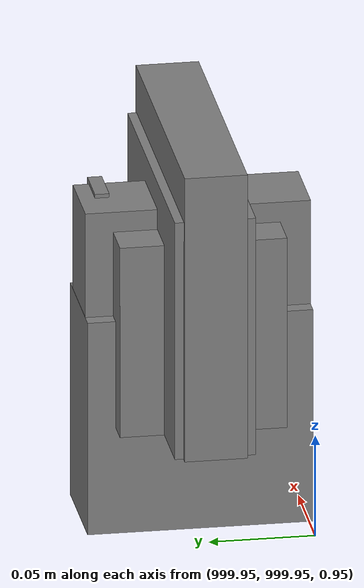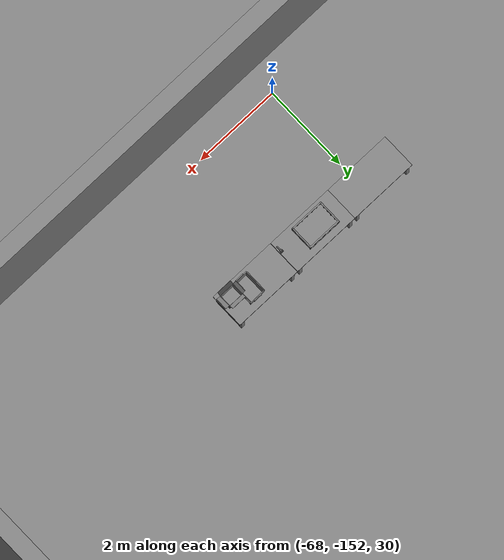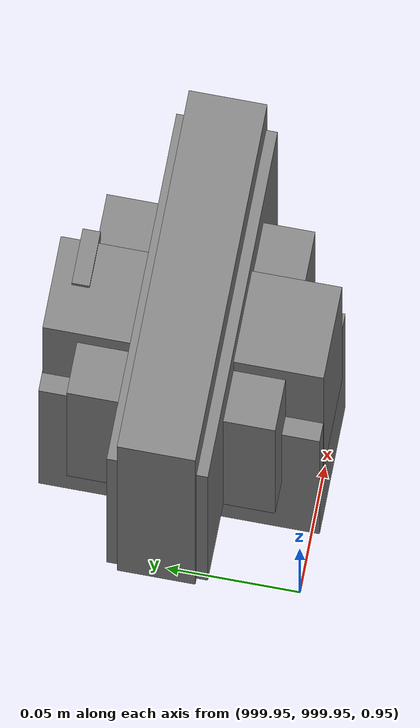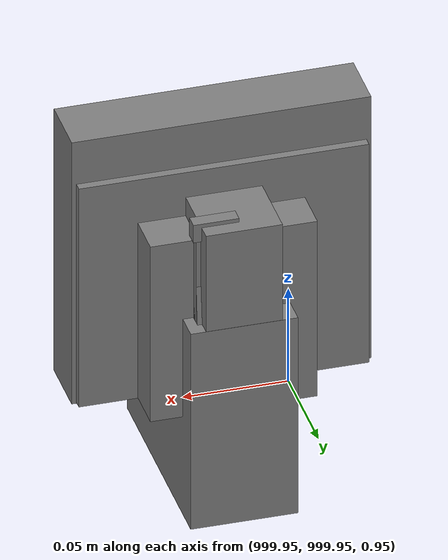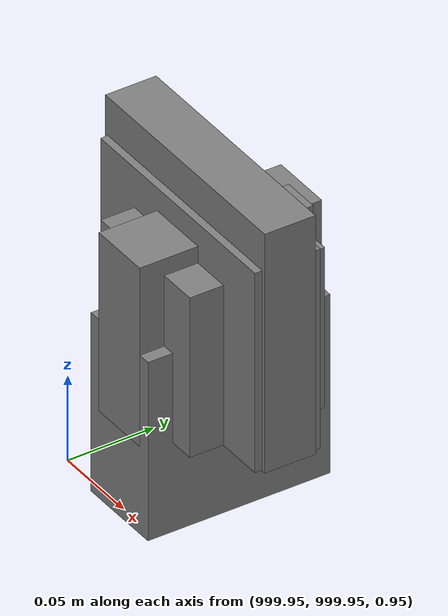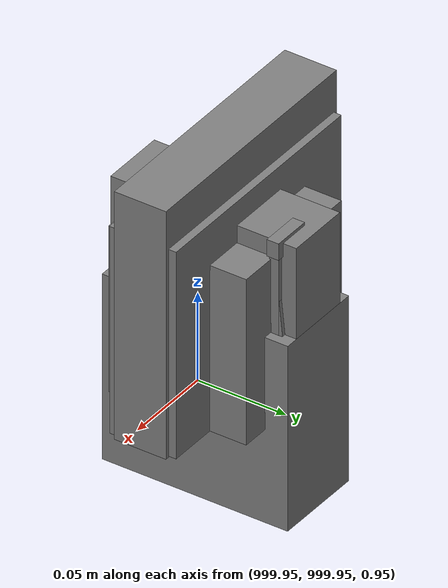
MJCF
<mujoco>
    <option gravity="0.000000000 0.000000000 -9.810000420" timestep="0.0049999999" integrator="implicitfast" density="1.225" viscosity="1.8000001e-05" noslip_iterations="10" iterations="100" sdf_iterations="50">
        <flag multiccd="disable"/>
    </option>
    <size memory="1000M"/>
    <compiler coordinate="local"/>
    <worldbody>
        <light cutoff="30" pos="0 1 1" dir="0 -1 -2"/>
        <light cutoff="30" pos="0 -1 1" dir="0 1 -2"/>
        <body pos="1000.000000000 999.999938965 1.000000000" euler="0.000000000 0.000000000 180.000000000" name="openloong_gripper_2f85_fix_base_usda_intelcore_i5">
            <geom contype="1" conaffinity="1" density="1000" type="box" material="" rgba="0.500000000 0.500000000 0.500000000 1.000000000" solimp="0.899999976 0.949999988 0.001000000" friction="1.000000000 0.005000000 0.000100000" solref="0.020000000 1.000000000" margin="0" condim="3" group="0" pos="0.000000000 0.000000000 0.051722717" quat="0.707106709 0.000000000 0.000000000 -0.707106769" size="0.052800000 0.018080002 0.052800000" name="openloong_gripper_2f85_fix_base_usda_geom_1238A77E_7106_4A2A_97D8_C4AEE4670EE0"/>
            <freejoint name="openloong_gripper_2f85_fix_base_usda_intelcore_i5_joint"/>
            <site size="0.005000000 0.005000000 0.005000000" rgba="0.500000000 0.500000000 0.500000000 1.000000000" pos="0.000000000 0.000000000 0.000000000" quat="0.999961913 0.008726534 0.000000000 0.000000000" group="0" type="sphere" name="openloong_gripper_2f85_fix_base_usda_intelcore_i5site"/>
        </body>
        <body pos="-66.284690857 -148.899032593 31.169652939" euler="142.261764526 -56.518157959 -154.309066772" mocap="true" name="spotlight5_SpotLight"/>
        <body pos="1000.000000000 1000.000000000 1.000000000" euler="0.000011953 0.000005123 -179.999984741" name="openloong_gripper_2f85_fix_base_usda_intel_box">
            <geom contype="1" conaffinity="1" density="1000" type="box" material="" rgba="0.500000000 0.500000000 0.500000000 1.000000000" solimp="0.899999976 0.949999988 0.001000000" friction="1.000000000 0.005000000 0.000100000" solref="0.020000000 1.000000000" margin="0" condim="3" group="0" pos="0.000000000 -0.000067139 0.000082284" quat="0.707106709 0.000000225 0.000000253 0.707106650" size="0.052800003 0.025300000 0.052800003" name="openloong_gripper_2f85_fix_base_usda_geom_675C5E44_5CC4_4226_90FE_8F737975355F"/>
            <freejoint name="openloong_gripper_2f85_fix_base_usda_intel_box_joint"/>
            <site size="0.005000000 0.005000000 0.005000000" rgba="0.500000000 0.500000000 0.500000000 1.000000000" pos="0.000000000 0.000000000 0.000000000" quat="0.999961913 0.008726500 0.000000000 0.000000000" group="0" type="sphere" name="openloong_gripper_2f85_fix_base_usda_intel_boxsite"/>
        </body>
        <body pos="-66.246704102 -149.173736572 31.167602539" euler="146.693634033 39.287319183 122.137214661" mocap="true" name="spotlight6_SpotLight"/>
        <body pos="1000.000000000 1000.000000000 1.000000000" euler="0.000000000 0.000000000 180.000000000" name="openloong_gripper_2f85_fix_base_usda_wifi_box">
            <geom contype="1" conaffinity="1" density="1000" type="box" material="" rgba="0.500000000 0.500000000 0.500000000 1.000000000" solimp="0.899999976 0.949999988 0.001000000" friction="1.000000000 0.005000000 0.000100000" solref="0.020000000 1.000000000" margin="0" condim="3" group="0" pos="0.000000000 0.000000000 0.058978677" quat="0.000000000 0.000000047 0.000000000 1.000000000" size="0.068499997 0.018999999 0.059000000" name="openloong_gripper_2f85_fix_base_usda_geom_34DBDE4F_4935_4591_903C_2027E2A1118B"/>
            <freejoint name="openloong_gripper_2f85_fix_base_usda_wifi_box_joint"/>
            <site size="0.005000000 0.005000000 0.005000000" rgba="0.500000000 0.500000000 0.500000000 1.000000000" pos="0.000000000 0.000000000 0.000000000" quat="0.999961913 0.008726500 0.000000000 0.000000000" group="0" type="sphere" name="openloong_gripper_2f85_fix_base_usda_wifi_boxsite"/>
        </body>
        <body pos="-66.228759766 -149.108947754 31.170265198" euler="-150.978729248 63.017536163 -22.806987762" mocap="true" name="spotlight2_SpotLight"/>
        <body pos="1000.000000000 1000.000000000 1.000000000" euler="0.000000000 0.000000000 180.000000000" name="openloong_gripper_2f85_fix_base_usda_cpu_fan">
            <geom contype="1" conaffinity="1" density="1000" type="box" material="" rgba="0.500000000 0.500000000 0.500000000 1.000000000" solimp="0.899999976 0.949999988 0.001000000" friction="1.000000000 0.005000000 0.000100000" solref="0.020000000 1.000000000" margin="0" condim="3" group="0" pos="0.000000000 0.000000000 0.070034981" quat="0.000000000 0.000000000 0.000000000 1.000000000" size="0.070700005 0.014699999 0.070700005" name="openloong_gripper_2f85_fix_base_usda_geom_0E42F059_A40B_496D_A165_BEAA57AD6DD0"/>
            <freejoint name="openloong_gripper_2f85_fix_base_usda_cpu_fan_joint"/>
            <site size="0.005000000 0.005000000 0.005000000" rgba="0.500000000 0.500000000 0.500000000 1.000000000" pos="0.000000000 0.000000000 0.000000000" quat="0.999961913 0.008726535 0.000000000 0.000000000" group="0" type="sphere" name="openloong_gripper_2f85_fix_base_usda_cpu_fancsite"/>
        </body>
        <body pos="1000.000000000 1000.000000000 1.000000000" euler="0.000000000 0.000000000 180.000000000" name="openloong_gripper_2f85_fix_base_usda_battery_01">
            <geom contype="1" conaffinity="1" density="1000" type="box" material="" rgba="0.500000000 0.500000000 0.500000000 1.000000000" solimp="0.899999976 0.949999988 0.001000000" friction="1.000000000 0.005000000 0.000100000" solref="0.020000000 1.000000000" margin="0" condim="3" group="0" pos="-0.011123657 -0.041940309 0.101691343" quat="1.000000000 0.000000000 0.000000000 0.000000000" size="0.010800000 0.003375000 0.004725000" name="openloong_gripper_2f85_fix_base_usda_geom_6709AB79_C5F4_4C00_AC98_B5D3AEC0A96B"/>
            <geom contype="1" conaffinity="1" density="1000" type="box" material="" rgba="0.500000000 0.500000000 0.500000000 1.000000000" solimp="0.899999976 0.949999988 0.001000000" friction="1.000000000 0.005000000 0.000100000" solref="0.020000000 1.000000000" margin="0" condim="3" group="0" pos="-0.010876465 -0.044247437 0.047066893" quat="0.998702705 -0.050920475 0.000000000 0.000000000" size="0.009450001 0.002700000 0.024975000" name="openloong_gripper_2f85_fix_base_usda_geom_1BA45401_912C_42EF_B8AA_F1B937648697"/>
            <geom contype="1" conaffinity="1" density="1000" type="box" material="" rgba="0.500000000 0.500000000 0.500000000 1.000000000" solimp="0.899999976 0.949999988 0.001000000" friction="1.000000000 0.005000000 0.000100000" solref="0.020000000 1.000000000" margin="0" condim="3" group="0" pos="-0.001235962 -0.000659180 0.047381196" quat="1.000000000 0.000000000 0.000000000 0.000000000" size="0.039420001 0.039150000 0.047250003" name="openloong_gripper_2f85_fix_base_usda_geom_285F4345_CE40_40D8_A4CA_21FABEF682E6"/>
            <geom contype="1" conaffinity="1" density="1000" type="box" material="" rgba="0.500000000 0.500000000 0.500000000 1.000000000" solimp="0.899999976 0.949999988 0.001000000" friction="1.000000000 0.005000000 0.000100000" solref="0.020000000 1.000000000" margin="0" condim="3" group="0" pos="-0.010876465 -0.039138794 0.009851727" quat="1.000000000 0.000000000 0.000000000 0.000000000" size="0.009450001 0.010800000 0.013500000" name="openloong_gripper_2f85_fix_base_usda_geom_58D1E625_280F_451C_8C60_CCF674F587F5"/>
            <geom contype="1" conaffinity="1" density="1000" type="box" material="" rgba="0.500000000 0.500000000 0.500000000 1.000000000" solimp="0.899999976 0.949999988 0.001000000" friction="1.000000000 0.005000000 0.000100000" solref="0.020000000 1.000000000" margin="0" condim="3" group="0" pos="-0.010876465 -0.041528322 0.071508206" quat="1.000000000 0.000000000 0.000000000 0.000000000" size="0.009450001 0.002700000 0.027000001" name="openloong_gripper_2f85_fix_base_usda_geom_976C6A8A_9AC6_4D58_8BCB_4146173CB69B"/>
            <freejoint name="openloong_gripper_2f85_fix_base_usda_battery_01_joint"/>
            <site size="0.005000000 0.005000000 0.005000000" rgba="0.500000000 0.500000000 0.500000000 1.000000000" pos="0.000000000 0.000000000 0.000000000" quat="0.999961913 0.008726500 0.000000000 0.000000000" group="0" type="sphere" name="openloong_gripper_2f85_fix_base_usda_battery_01site"/>
        </body>
        <body pos="-64.866622925 -149.383972168 30.183746338" euler="89.999984741 89.999946594 0.000000000" name="openloong_gripper_2f85_fix_base_usda_bluebox_01">
            <geom contype="1" conaffinity="1" density="1000" type="box" material="" rgba="0.500000000 0.500000000 0.500000000 1.000000000" solimp="0.899999976 0.949999988 0.001000000" friction="1.000000000 0.005000000 0.000100000" solref="0.020000000 1.000000000" margin="0" condim="3" group="0" pos="0.276580811 0.187225342 0.000068665" quat="0.707106948 0.000077471 0.707106352 0.000077486" size="0.100000001 0.057999998 0.010000000" name="openloong_gripper_2f85_fix_base_usda_geom_2D1CA8D4_EB9E_450A_95D6_1ADB4EEABC2A"/>
            <geom contype="1" conaffinity="1" density="1000" type="box" material="" rgba="0.500000000 0.500000000 0.500000000 1.000000000" solimp="0.899999976 0.949999988 0.001000000" friction="1.000000000 0.005000000 0.000100000" solref="0.020000000 1.000000000" margin="0" condim="3" group="0" pos="0.000000000 0.002883911 0.000000000" quat="0.999999881 0.000000000 0.000000000 0.000000000" size="0.254000008 0.003000000 0.172000006" name="openloong_gripper_2f85_fix_base_usda_geom_EEED55C1_DFA1_425F_A0AB_9EB36164680D"/>
            <geom contype="1" conaffinity="1" density="1000" type="box" material="" rgba="0.500000000 0.500000000 0.500000000 1.000000000" solimp="0.899999976 0.949999988 0.001000000" friction="1.000000000 0.005000000 0.000100000" solref="0.020000000 1.000000000" margin="0" condim="3" group="0" pos="0.000000000 0.124874115 0.173484802" quat="0.999796331 0.020176515 -0.000000015 0.000000030" size="0.259999990 0.119999997 0.007000000" name="openloong_gripper_2f85_fix_base_usda_geom_608F04D0_1905_4562_B17A_402125E0799D"/>
            <geom contype="1" conaffinity="1" density="1000" type="box" material="" rgba="0.500000000 0.500000000 0.500000000 1.000000000" solimp="0.899999976 0.949999988 0.001000000" friction="1.000000000 0.005000000 0.000100000" solref="0.020000000 1.000000000" margin="0" condim="3" group="0" pos="0.000000000 0.124874115 -0.173469543" quat="0.999796331 -0.020176545 -0.000000015 0.000000000" size="0.259999990 0.119999997 0.007000000" name="openloong_gripper_2f85_fix_base_usda_geom_6E846455_7A4E_4060_88D5_0DA5B3B7225B"/>
            <geom contype="1" conaffinity="1" density="1000" type="box" material="" rgba="0.500000000 0.500000000 0.500000000 1.000000000" solimp="0.899999976 0.949999988 0.001000000" friction="1.000000000 0.005000000 0.000100000" solref="0.020000000 1.000000000" margin="0" condim="3" group="0" pos="0.000000000 0.214008331 0.188980103" quat="0.999912977 0.013176724 0.000000015 0.000000000" size="0.259999990 0.029999999 0.012500000" name="openloong_gripper_2f85_fix_base_usda_geom_B20D7344_A139_4165_AB22_7088DBE85DB3"/>
            <geom contype="1" conaffinity="1" density="1000" type="box" material="" rgba="0.500000000 0.500000000 0.500000000 1.000000000" solimp="0.899999976 0.949999988 0.001000000" friction="1.000000000 0.005000000 0.000100000" solref="0.020000000 1.000000000" margin="0" condim="3" group="0" pos="-0.258361816 0.125289917 0.001876831" quat="0.702796936 -0.020792112 0.710783124 0.020769298" size="0.189999998 0.119999997 0.009000000" name="openloong_gripper_2f85_fix_base_usda_geom_E08E4628_CB16_4684_B589_E2F1C704A42E"/>
            <geom contype="1" conaffinity="1" density="1000" type="box" material="" rgba="0.500000000 0.500000000 0.500000000 1.000000000" solimp="0.899999976 0.949999988 0.001000000" friction="1.000000000 0.005000000 0.000100000" solref="0.020000000 1.000000000" margin="0" condim="3" group="0" pos="0.000000000 0.214008331 -0.188980103" quat="0.999912977 -0.013176769 0.000000030 0.000000015" size="0.259999990 0.029999999 0.012500000" name="openloong_gripper_2f85_fix_base_usda_geom_5019E799_D4BA_4684_BDCA_B09B8CB01DFD"/>
            <geom contype="1" conaffinity="1" density="1000" type="box" material="" rgba="0.500000000 0.500000000 0.500000000 1.000000000" solimp="0.899999976 0.949999988 0.001000000" friction="1.000000000 0.005000000 0.000100000" solref="0.020000000 1.000000000" margin="0" condim="3" group="0" pos="-0.276611328 0.187225342 0.000068665" quat="0.707106650 0.000077441 0.707106709 0.000077456" size="0.100000001 0.057999998 0.010000000" name="openloong_gripper_2f85_fix_base_usda_geom_57C359C5_A238_4025_99ED_1628DC2FD34C"/>
            <geom contype="1" conaffinity="1" density="1000" type="box" material="" rgba="0.500000000 0.500000000 0.500000000 1.000000000" solimp="0.899999976 0.949999988 0.001000000" friction="1.000000000 0.005000000 0.000100000" solref="0.020000000 1.000000000" margin="0" condim="3" group="0" pos="0.258331299 0.125289917 0.001876831" quat="0.702851415 0.018856421 0.710823774 -0.019329369" size="0.189999998 0.119999997 0.009000000" name="openloong_gripper_2f85_fix_base_usda_geom_A8D9F989_6F55_4E3B_8C23_0B6D2C471578"/>
            <freejoint name="openloong_gripper_2f85_fix_base_usda_bluebox_01_joint"/>
            <site size="0.005000000 0.005000000 0.005000000" rgba="0.500000000 0.500000000 0.500000000 1.000000000" pos="0.000000000 0.000000000 0.000000000" quat="0.999961913 0.008726534 0.000000000 0.000000000" group="0" type="sphere" name="openloong_gripper_2f85_fix_base_usda_bluebox_01site"/>
        </body>
        <body pos="-64.496299744 -149.491867065 30.235729218" euler="0.000000000 0.000000000 89.999946594" name="openloong_gripper_2f85_fix_base_usda_cardboardbox_01">
            <geom contype="1" conaffinity="1" density="1000" type="box" material="" rgba="0.500000000 0.500000000 0.500000000 1.000000000" solimp="0.899999976 0.949999988 0.001000000" friction="1.000000000 0.005000000 0.000100000" solref="0.020000000 1.000000000" margin="0" condim="3" group="0" pos="-0.003166199 -0.004086494 0.005052090" quat="1.000000000 0.000000000 0.000000000 0.000000000" size="0.142499998 0.177500010 0.005000000" name="openloong_gripper_2f85_fix_base_usda_geom_644FE7B4_EFF1_40CF_B402_2F51FDBE8A19"/>
            <geom contype="1" conaffinity="1" density="1000" type="box" material="" rgba="0.500000000 0.500000000 0.500000000 1.000000000" solimp="0.899999976 0.949999988 0.001000000" friction="1.000000000 0.005000000 0.000100000" solref="0.020000000 1.000000000" margin="0" condim="3" group="0" pos="-0.003166199 0.170316696 0.150570869" quat="1.000000000 0.000000000 0.000000000 0.000000000" size="0.142499998 0.005000000 0.149999991" name="openloong_gripper_2f85_fix_base_usda_geom_4360F625_EEC4_4F37_9333_2C8F707138F4"/>
            <geom contype="1" conaffinity="1" density="1000" type="box" material="" rgba="0.500000000 0.500000000 0.500000000 1.000000000" solimp="0.899999976 0.949999988 0.001000000" friction="1.000000000 0.005000000 0.000100000" solref="0.020000000 1.000000000" margin="0" condim="3" group="0" pos="-0.147399902 -0.005307198 0.150570869" quat="1.000000000 0.000000000 0.000000000 0.000000000" size="0.005000000 0.177500010 0.149999991" name="openloong_gripper_2f85_fix_base_usda_geom_8A6FFCEA_7FB6_45B7_A87E_DA2C93F4F72B"/>
            <geom contype="1" conaffinity="1" density="1000" type="box" material="" rgba="0.500000000 0.500000000 0.500000000 1.000000000" solimp="0.899999976 0.949999988 0.001000000" friction="1.000000000 0.005000000 0.000100000" solref="0.020000000 1.000000000" margin="0" condim="3" group="0" pos="0.140275955 -0.005307198 0.150570869" quat="1.000000000 0.000000000 0.000000000 0.000000000" size="0.005000000 0.177500010 0.149999991" name="openloong_gripper_2f85_fix_base_usda_geom_3DC1AC92_D3EB_4E15_8199_69A37BA4A334"/>
            <geom contype="1" conaffinity="1" density="1000" type="box" material="" rgba="0.500000000 0.500000000 0.500000000 1.000000000" solimp="0.899999976 0.949999988 0.001000000" friction="1.000000000 0.005000000 0.000100000" solref="0.020000000 1.000000000" margin="0" condim="3" group="0" pos="-0.003166199 -0.181550980 0.150570869" quat="1.000000000 0.000000000 0.000000000 0.000000000" size="0.142499998 0.005000000 0.149999991" name="openloong_gripper_2f85_fix_base_usda_geom_31D720A5_5DD0_4DF9_8C80_65739C7ECFA8"/>
            <freejoint name="openloong_gripper_2f85_fix_base_usda_cardboardbox_01_joint"/>
            <site size="0.005000000 0.005000000 0.005000000" rgba="0.500000000 0.500000000 0.500000000 1.000000000" pos="0.000000000 0.000000000 0.000000000" quat="0.999961913 0.008726535 0.000000000 0.000000000" group="0" type="sphere" name="openloong_gripper_2f85_fix_base_usda_site_C01787DA_E5C8_4E5D_81FC_F409F75906C5"/>
            <body pos="0.139160156 -0.004048347 0.301930904" euler="-179.999954224 49.383502960 179.999954224" name="openloong_gripper_2f85_fix_base_usda_A1_006">
                <geom contype="1" conaffinity="1" density="1000" type="box" material="" rgba="0.500000000 0.500000000 0.500000000 1.000000000" solimp="0.899999976 0.949999988 0.001000000" friction="1.000000000 0.005000000 0.000100000" solref="0.020000000 1.000000000" margin="0" condim="3" group="0" pos="-0.071587563 0.000009537 0.001745224" quat="0.999999881 0.000000000 0.000000000 0.000000000" size="0.071249999 0.179999992 0.002500000" name="openloong_gripper_2f85_fix_base_usda_geom_6CC2D999_F0CE_4D3B_981F_987AA443566E"/>
                <joint armature="0" stiffness="0.07" damping="0.0099999998" axis="0.000000 1.000000 0.000000" type="hinge" name="openloong_gripper_2f85_fix_base_usda_A1_006"/>
            </body>
            <body pos="-0.145902634 -0.004086494 0.301938057" euler="-180.000000000 -60.000011444 -180.000000000" name="openloong_gripper_2f85_fix_base_usda_A2_006">
                <geom contype="1" conaffinity="1" density="1000" type="box" material="" rgba="0.500000000 0.500000000 0.500000000 1.000000000" solimp="0.899999976 0.949999988 0.001000000" friction="1.000000000 0.005000000 0.000100000" solref="0.020000000 1.000000000" margin="0" condim="3" group="0" pos="0.071268082 0.000009537 0.002717972" quat="0.000002921 0.000000000 -0.000000030 0.999999881" size="0.071249999 0.179999992 0.002500000" name="openloong_gripper_2f85_fix_base_usda_geom_D15738F9_F71E_4124_9D17_68186D3ADB8F"/>
                <joint armature="0" stiffness="0.07" damping="0.0099999998" axis="0.000000 1.000000 0.000000" type="hinge" name="openloong_gripper_2f85_fix_base_usda_A2_006"/>
            </body>
            <body pos="-0.003385544 0.175991058 0.301930904" euler="-125.858116150 -0.000004561 0.000002331" name="openloong_gripper_2f85_fix_base_usda_B2_006">
                <geom contype="1" conaffinity="1" density="1000" type="box" material="" rgba="0.500000000 0.500000000 0.500000000 1.000000000" solimp="0.899999976 0.949999988 0.001000000" friction="1.000000000 0.005000000 0.000100000" solref="0.020000000 1.000000000" margin="0" condim="3" group="0" pos="0.000009537 -0.070939064 -0.002470016" quat="0.999614120 0.027776197 -0.000000015 0.000000030" size="0.137500003 0.064999998 0.005000000" name="openloong_gripper_2f85_fix_base_usda_geom_9EC03742_817D_4295_BD1E_0AB2A1665A8B"/>
                <joint armature="0" stiffness="0.07" damping="0.0099999998" axis="1.000000 0.000000 0.000000" type="hinge" name="openloong_gripper_2f85_fix_base_usda_B2_006"/>
            </body>
            <body pos="-0.003385544 -0.184140205 0.301938057" euler="147.805557251 0.000000000 0.000000000" name="openloong_gripper_2f85_fix_base_usda_B1_006">
                <geom contype="1" conaffinity="1" density="1000" type="box" material="" rgba="0.500000000 0.500000000 0.500000000 1.000000000" solimp="0.899999976 0.949999988 0.001000000" friction="1.000000000 0.005000000 0.000100000" solref="0.020000000 1.000000000" margin="0" condim="3" group="0" pos="-0.000028610 0.070202351 -0.002703667" quat="0.999614179 -0.027776167 0.000000000 0.000000000" size="0.137500003 0.064999998 0.005000000" name="openloong_gripper_2f85_fix_base_usda_geom_DD9AB133_DF96_4192_8E7A_58185EDE607D"/>
                <joint armature="0" stiffness="0.07" damping="0.0099999998" axis="1.000000 0.000000 0.000000" type="hinge" name="openloong_gripper_2f85_fix_base_usda_B1_006"/>
            </body>
        </body>
        <body pos="-65.882858276 -149.481979370 30.229999542" euler="-64.487716675 0.000000000 0.000000000" name="openloong_gripper_2f85_fix_base_usda_Barcode">
            <geom contype="1" conaffinity="1" density="1000" type="box" material="" rgba="0.500000000 0.500000000 0.500000000 1.000000000" solimp="0.899999976 0.949999988 0.001000000" friction="1.000000000 0.005000000 0.000100000" solref="0.020000000 1.000000000" margin="0" condim="3" group="0" pos="0.000000000 0.013038635 0.001419067" quat="0.000000000 0.000000000 0.000000000 1.000000119" size="0.034000002 0.010000000 0.017999999" name="openloong_gripper_2f85_fix_base_usda_geom_2C83A950_EB9A_4307_9796_6060938DE881"/>
            <geom contype="1" conaffinity="1" density="1000" type="box" material="" rgba="0.500000000 0.500000000 0.500000000 1.000000000" solimp="0.899999976 0.949999988 0.001000000" friction="1.000000000 0.005000000 0.000100000" solref="0.020000000 1.000000000" margin="0" condim="3" group="0" pos="0.000000000 -0.035301208 -0.007095337" quat="0.000000000 0.000000000 -0.043619365 0.999048233" size="0.028999999 0.010000000 0.020000000" name="openloong_gripper_2f85_fix_base_usda_geom_B3EEF1B3_C5B3_4B31_A9D6_E1C386E6B2A0"/>
            <geom contype="1" conaffinity="1" density="1000" type="box" material="" rgba="0.500000000 0.500000000 0.500000000 1.000000000" solimp="0.899999976 0.949999988 0.001000000" friction="1.000000000 0.005000000 0.000100000" solref="0.020000000 1.000000000" margin="0" condim="3" group="0" pos="0.000000000 -0.043411255 -0.011749268" quat="0.922262907 0.386563420 0.000000000 0.000000000" size="0.026000001 0.010000000 0.020000000" name="openloong_gripper_2f85_fix_base_usda_geom_FED84CFD_2528_432A_83BE_758C468902FA"/>
            <geom contype="1" conaffinity="1" density="1000" type="box" material="" rgba="0.500000000 0.500000000 0.500000000 1.000000000" solimp="0.899999976 0.949999988 0.001000000" friction="1.000000000 0.005000000 0.000100000" solref="0.020000000 1.000000000" margin="0" condim="3" group="0" pos="0.000000000 -0.016967773 -0.031860352" quat="0.000000000 0.000000000 0.000000000 1.000000119" size="0.008000000 0.010000000 0.013000000" name="openloong_gripper_2f85_fix_base_usda_geom_D50B739B_4D0E_4B48_B7F5_275748287099"/>
            <geom contype="1" conaffinity="1" density="1000" type="box" material="" rgba="0.500000000 0.500000000 0.500000000 1.000000000" solimp="0.899999976 0.949999988 0.001000000" friction="1.000000000 0.005000000 0.000100000" solref="0.020000000 1.000000000" margin="0" condim="3" group="0" pos="0.000000000 -0.001869202 0.000312805" quat="0.953716993 0.300705761 0.000000000 0.000000000" size="0.032000002 0.010000000 0.018999999" name="openloong_gripper_2f85_fix_base_usda_geom_3BC36A2E_CC8E_493F_8B69_CA0CF02FD52C"/>
            <geom contype="1" conaffinity="1" density="1000" type="box" material="" rgba="0.500000000 0.500000000 0.500000000 1.000000000" solimp="0.899999976 0.949999988 0.001000000" friction="1.000000000 0.005000000 0.000100000" solref="0.020000000 1.000000000" margin="0" condim="3" group="0" pos="0.000000000 -0.019531250 -0.003173828" quat="0.953716993 0.300705761 0.000000000 0.000000000" size="0.030999999 0.010000000 0.020000000" name="openloong_gripper_2f85_fix_base_usda_geom_E57B4CBF_24C4_4F2A_893C_D6E2B9F0F6AE"/>
            <geom contype="1" conaffinity="1" density="1000" type="box" material="" rgba="0.500000000 0.500000000 0.500000000 1.000000000" solimp="0.899999976 0.949999988 0.001000000" friction="1.000000000 0.005000000 0.000100000" solref="0.020000000 1.000000000" margin="0" condim="3" group="0" pos="0.000000000 -0.035301208 -0.007095337" quat="0.953716993 0.300705761 0.000000000 0.000000000" size="0.028999999 0.010000000 0.020000000" name="openloong_gripper_2f85_fix_base_usda_geom_B24F367C_04B6_4102_AB61_DFB62E6A22BC"/>
            <geom contype="1" conaffinity="1" density="1000" type="box" material="" rgba="0.500000000 0.500000000 0.500000000 1.000000000" solimp="0.899999976 0.949999988 0.001000000" friction="1.000000000 0.005000000 0.000100000" solref="0.020000000 1.000000000" margin="0" condim="3" group="0" pos="0.000000000 -0.042617798 -0.071121216" quat="0.000000000 0.000000000 0.000000000 1.000000119" size="0.013000000 0.021000000 0.059999999" name="openloong_gripper_2f85_fix_base_usda_geom_7D951F25_DE0E_4A87_A55D_F40DE2BDF7E6"/>
            <freejoint name="openloong_gripper_2f85_fix_base_usda_Barcode_joint"/>
            <site size="0.005000000 0.005000000 0.005000000" rgba="0.500000000 0.500000000 0.500000000 1.000000000" pos="0.000000000 0.000000000 0.000000000" quat="1.000000000 0.000000000 0.000000000 0.000000000" group="0" type="sphere" name="openloong_gripper_2f85_fix_base_usda_Barcode_site"/>
        </body>
        <body pos="-66.745018005 -149.392349243 30.184000015" euler="0.000000000 0.000000000 89.999946594" name="[22333012066871]_Basket_01">
            <geom contype="1" conaffinity="1" density="1000" type="box" material="" rgba="0.500000000 0.500000000 0.500000000 1.000000000" solimp="0.899999976 0.949999988 0.001000000" friction="1.000000000 0.005000000 0.000100000" solref="0.020000000 1.000000000" margin="0" condim="3" group="0" pos="-0.052425385 0.389207840 0.089787483" quat="0.707107008 0.000000000 0.000000000 0.707106411" size="0.014249999 0.014249999 0.059999999" name="[22333012066871]_geom_87EA8EFA_9B98_4CAB_A023_07409A82F111"/>
            <geom contype="1" conaffinity="1" density="1000" type="box" material="" rgba="0.500000000 0.500000000 0.500000000 1.000000000" solimp="0.899999976 0.949999988 0.001000000" friction="1.000000000 0.005000000 0.000100000" solref="0.020000000 1.000000000" margin="0" condim="3" group="0" pos="0.264015198 -0.133043289 0.089787483" quat="0.707107008 0.000000000 0.000000000 0.707106411" size="0.014249999 0.014249999 0.059999999" name="[22333012066871]_geom_A972081A_956A_4728_9B4D_D3FD677A30F6"/>
            <geom contype="1" conaffinity="1" density="1000" type="box" material="" rgba="0.500000000 0.500000000 0.500000000 1.000000000" solimp="0.899999976 0.949999988 0.001000000" friction="1.000000000 0.005000000 0.000100000" solref="0.020000000 1.000000000" margin="0" condim="3" group="0" pos="-0.264015198 -0.265548706 0.089793205" quat="0.707107008 0.000000000 0.000000000 0.707106411" size="0.014249999 0.014249999 0.059999999" name="[22333012066871]_geom_C69EF7D0_4BBF_4635_988A_C36C79FF1992"/>
            <geom contype="1" conaffinity="1" density="1000" type="box" material="" rgba="0.500000000 0.500000000 0.500000000 1.000000000" solimp="0.899999976 0.949999988 0.001000000" friction="1.000000000 0.005000000 0.000100000" solref="0.020000000 1.000000000" margin="0" condim="3" group="0" pos="-0.160263062 -0.389322281 0.089793205" quat="0.707107008 0.000000000 0.000000000 0.707106411" size="0.014249999 0.014249999 0.059999999" name="[22333012066871]_geom_CE61A4AB_0731_4EAE_A248_42B2EF4FEBA4"/>
            <geom contype="1" conaffinity="1" density="1000" type="box" material="" rgba="0.500000000 0.500000000 0.500000000 1.000000000" solimp="0.899999976 0.949999988 0.001000000" friction="1.000000000 0.005000000 0.000100000" solref="0.020000000 1.000000000" margin="0" condim="3" group="0" pos="0.162265778 -0.389322281 0.089787483" quat="0.707107008 0.000000000 0.000000000 0.707106411" size="0.014249999 0.014249999 0.059999999" name="[22333012066871]_geom_52BFC413_320B_4447_A1BF_F2DE70147E07"/>
            <geom contype="1" conaffinity="1" density="1000" type="box" material="" rgba="0.500000000 0.500000000 0.500000000 1.000000000" solimp="0.899999976 0.949999988 0.001000000" friction="1.000000000 0.005000000 0.000100000" solref="0.020000000 1.000000000" margin="0" condim="3" group="0" pos="0.264015198 0.389207840 0.089787483" quat="0.707107008 0.000000000 0.000000000 0.707106411" size="0.014249999 0.014249999 0.059999999" name="[22333012066871]_geom_EFEE1EB1_61F2_40C7_845D_CBA61AD1A99B"/>
            <geom contype="1" conaffinity="1" density="1000" type="box" material="" rgba="0.500000000 0.500000000 0.500000000 1.000000000" solimp="0.899999976 0.949999988 0.001000000" friction="1.000000000 0.005000000 0.000100000" solref="0.020000000 1.000000000" margin="0" condim="3" group="0" pos="-0.264015198 -0.133043289 0.089793205" quat="0.707107008 0.000000000 0.000000000 0.707106411" size="0.014249999 0.014249999 0.059999999" name="[22333012066871]_geom_31B30BD9_82CA_45BE_882E_29D5A83A8BD2"/>
            <geom contype="1" conaffinity="1" density="1000" type="box" material="" rgba="0.500000000 0.500000000 0.500000000 1.000000000" solimp="0.899999976 0.949999988 0.001000000" friction="1.000000000 0.005000000 0.000100000" solref="0.020000000 1.000000000" margin="0" condim="3" group="0" pos="-0.264026642 0.269256592 0.089793205" quat="0.707107008 0.000000000 0.000000000 0.707106411" size="0.014249999 0.014249999 0.059999999" name="[22333012066871]_geom_11210EAF_3789_4452_89BD_33EFF8E63DE1"/>
            <geom contype="1" conaffinity="1" density="1000" type="box" material="" rgba="0.500000000 0.500000000 0.500000000 1.000000000" solimp="0.899999976 0.949999988 0.001000000" friction="1.000000000 0.005000000 0.000100000" solref="0.020000000 1.000000000" margin="0" condim="3" group="0" pos="0.054462433 0.389207840 0.089787483" quat="0.707107008 0.000000000 0.000000000 0.707106411" size="0.014249999 0.014249999 0.059999999" name="[22333012066871]_geom_B5328E88_611A_44F4_9E55_13F1C47D0222"/>
            <geom contype="1" conaffinity="1" density="1000" type="box" material="" rgba="0.500000000 0.500000000 0.500000000 1.000000000" solimp="0.899999976 0.949999988 0.001000000" friction="1.000000000 0.005000000 0.000100000" solref="0.020000000 1.000000000" margin="0" condim="3" group="0" pos="0.054462433 -0.389322281 0.089787483" quat="0.707107008 0.000000000 0.000000000 0.707106411" size="0.014249999 0.014249999 0.059999999" name="[22333012066871]_geom_1C318A62_6492_4444_BAF6_221562CC783A"/>
            <geom contype="1" conaffinity="1" density="1000" type="box" material="" rgba="0.500000000 0.500000000 0.500000000 1.000000000" solimp="0.899999976 0.949999988 0.001000000" friction="1.000000000 0.005000000 0.000100000" solref="0.020000000 1.000000000" margin="0" condim="3" group="0" pos="0.264015198 0.269256592 0.089793205" quat="0.707107008 0.000000000 0.000000000 0.707106411" size="0.014249999 0.014249999 0.059999999" name="[22333012066871]_geom_5297F12A_8658_4388_9B73_A5E796CC6B70"/>
            <geom contype="1" conaffinity="1" density="1000" type="box" material="" rgba="0.500000000 0.500000000 0.500000000 1.000000000" solimp="0.899999976 0.949999988 0.001000000" friction="1.000000000 0.005000000 0.000100000" solref="0.020000000 1.000000000" margin="0" condim="3" group="0" pos="0.264015198 -0.389322281 0.089787483" quat="0.707107008 0.000000000 0.000000000 0.707106411" size="0.014249999 0.014249999 0.059999999" name="[22333012066871]_geom_1B6A5A14_4C7B_4FEE_93F5_7E189A3096E8"/>
            <geom contype="1" conaffinity="1" density="1000" type="box" material="" rgba="0.500000000 0.500000000 0.500000000 1.000000000" solimp="0.899999976 0.949999988 0.001000000" friction="1.000000000 0.005000000 0.000100000" solref="0.020000000 1.000000000" margin="0" condim="3" group="0" pos="0.000000000 0.000000000 0.015998840" quat="0.707107008 0.000000000 0.000000000 0.707106411" size="0.403499991 0.279000014 0.015750000" name="[22333012066871]_geom_C969C61E_5255_438B_B723_36FC6CA1D2A5"/>
            <geom contype="1" conaffinity="1" density="1000" type="box" material="" rgba="0.500000000 0.500000000 0.500000000 1.000000000" solimp="0.899999976 0.949999988 0.001000000" friction="1.000000000 0.005000000 0.000100000" solref="0.020000000 1.000000000" margin="0" condim="3" group="0" pos="0.000000000 -0.389476776 0.163619041" quat="0.707107008 0.000000000 0.000000000 0.707106411" size="0.015000000 0.277500004 0.015750000" name="[22333012066871]_geom_09B45396_AD60_4D5B_A66A_632E364F77C2"/>
            <geom contype="1" conaffinity="1" density="1000" type="box" material="" rgba="0.500000000 0.500000000 0.500000000 1.000000000" solimp="0.899999976 0.949999988 0.001000000" friction="1.000000000 0.005000000 0.000100000" solref="0.020000000 1.000000000" margin="0" condim="3" group="0" pos="0.162265778 0.389207840 0.089787483" quat="0.707107008 0.000000000 0.000000000 0.707106411" size="0.014249999 0.014249999 0.059999999" name="[22333012066871]_geom_D75256B9_849D_472F_B76D_EA8F8F5B6F6F"/>
            <geom contype="1" conaffinity="1" density="1000" type="box" material="" rgba="0.500000000 0.500000000 0.500000000 1.000000000" solimp="0.899999976 0.949999988 0.001000000" friction="1.000000000 0.005000000 0.000100000" solref="0.020000000 1.000000000" margin="0" condim="3" group="0" pos="0.000000000 0.389471054 0.163619041" quat="0.707107008 0.000000000 0.000000000 0.707106411" size="0.015000000 0.277500004 0.015750000" name="[22333012066871]_geom_0068197A_246B_4B52_A9E7_0DD0BC766CBF"/>
            <geom contype="1" conaffinity="1" density="1000" type="box" material="" rgba="0.500000000 0.500000000 0.500000000 1.000000000" solimp="0.899999976 0.949999988 0.001000000" friction="1.000000000 0.005000000 0.000100000" solref="0.020000000 1.000000000" margin="0" condim="3" group="0" pos="-0.263511658 0.000000000 0.163619041" quat="0.707107008 0.000000000 0.000000000 0.707106411" size="0.403499991 0.015000000 0.015750000" name="[22333012066871]_geom_8174077E_BBFB_4D0E_B07E_BC7C85BCC15F"/>
            <geom contype="1" conaffinity="1" density="1000" type="box" material="" rgba="0.500000000 0.500000000 0.500000000 1.000000000" solimp="0.899999976 0.949999988 0.001000000" friction="1.000000000 0.005000000 0.000100000" solref="0.020000000 1.000000000" margin="0" condim="3" group="0" pos="-0.264015198 0.141334534 0.089793205" quat="0.707107008 0.000000000 0.000000000 0.707106411" size="0.014249999 0.014249999 0.059999999" name="[22333012066871]_geom_961C710A_1CE4_4CAD_9523_2134CF9D3B37"/>
            <geom contype="1" conaffinity="1" density="1000" type="box" material="" rgba="0.500000000 0.500000000 0.500000000 1.000000000" solimp="0.899999976 0.949999988 0.001000000" friction="1.000000000 0.005000000 0.000100000" solref="0.020000000 1.000000000" margin="0" condim="3" group="0" pos="0.264015198 -0.265548706 0.089787483" quat="0.707107008 0.000000000 0.000000000 0.707106411" size="0.014249999 0.014249999 0.059999999" name="[22333012066871]_geom_190824F0_5F32_4794_B2BC_A32BD264FA23"/>
            <geom contype="1" conaffinity="1" density="1000" type="box" material="" rgba="0.500000000 0.500000000 0.500000000 1.000000000" solimp="0.899999976 0.949999988 0.001000000" friction="1.000000000 0.005000000 0.000100000" solref="0.020000000 1.000000000" margin="0" condim="3" group="0" pos="-0.160263062 0.389207840 0.089787483" quat="0.707107008 0.000000000 0.000000000 0.707106411" size="0.014249999 0.014249999 0.059999999" name="[22333012066871]_geom_D43E611F_0D6E_49A6_84BE_6AF4E59C5FB8"/>
            <geom contype="1" conaffinity="1" density="1000" type="box" material="" rgba="0.500000000 0.500000000 0.500000000 1.000000000" solimp="0.899999976 0.949999988 0.001000000" friction="1.000000000 0.005000000 0.000100000" solref="0.020000000 1.000000000" margin="0" condim="3" group="0" pos="-0.052425385 -0.389322281 0.089787483" quat="0.707107008 0.000000000 0.000000000 0.707106411" size="0.014249999 0.014249999 0.059999999" name="[22333012066871]_geom_7CD81E5F_9AFB_4560_9EC0_4481404CEE5D"/>
            <geom contype="1" conaffinity="1" density="1000" type="box" material="" rgba="0.500000000 0.500000000 0.500000000 1.000000000" solimp="0.899999976 0.949999988 0.001000000" friction="1.000000000 0.005000000 0.000100000" solref="0.020000000 1.000000000" margin="0" condim="3" group="0" pos="-0.264026642 -0.389322281 0.089793205" quat="0.707107008 0.000000000 0.000000000 0.707106411" size="0.014249999 0.014249999 0.059999999" name="[22333012066871]_geom_7739C4CD_90C5_4A1B_ACA7_EAE7C4D4186F"/>
            <geom contype="1" conaffinity="1" density="1000" type="box" material="" rgba="0.500000000 0.500000000 0.500000000 1.000000000" solimp="0.899999976 0.949999988 0.001000000" friction="1.000000000 0.005000000 0.000100000" solref="0.020000000 1.000000000" margin="0" condim="3" group="0" pos="0.264015198 0.141334534 0.089787483" quat="0.707107008 0.000000000 0.000000000 0.707106411" size="0.014249999 0.014249999 0.059999999" name="[22333012066871]_geom_67D6AE5F_46C1_4DF8_803A_1979CBDBAA91"/>
            <geom contype="1" conaffinity="1" density="1000" type="box" material="" rgba="0.500000000 0.500000000 0.500000000 1.000000000" solimp="0.899999976 0.949999988 0.001000000" friction="1.000000000 0.005000000 0.000100000" solref="0.020000000 1.000000000" margin="0" condim="3" group="0" pos="-0.264015198 0.389207840 0.089793205" quat="0.707107008 0.000000000 0.000000000 0.707106411" size="0.014249999 0.014249999 0.059999999" name="[22333012066871]_geom_DBDCE660_E167_4B6F_BFA8_08D139CBB278"/>
            <geom contype="1" conaffinity="1" density="1000" type="box" material="" rgba="0.500000000 0.500000000 0.500000000 1.000000000" solimp="0.899999976 0.949999988 0.001000000" friction="1.000000000 0.005000000 0.000100000" solref="0.020000000 1.000000000" margin="0" condim="3" group="0" pos="0.264015198 0.004480362 0.089787483" quat="0.707107008 0.000000000 0.000000000 0.707106411" size="0.014249999 0.014249999 0.059999999" name="[22333012066871]_geom_9CA41DA5_6500_4B88_9446_177057DF04BE"/>
            <geom contype="1" conaffinity="1" density="1000" type="box" material="" rgba="0.500000000 0.500000000 0.500000000 1.000000000" solimp="0.899999976 0.949999988 0.001000000" friction="1.000000000 0.005000000 0.000100000" solref="0.020000000 1.000000000" margin="0" condim="3" group="0" pos="0.263694763 -0.000011444 0.163619041" quat="0.707107008 0.000000000 0.000000000 0.707106411" size="0.403499991 0.015000000 0.015750000" name="[22333012066871]_geom_382A4445_EC96_4227_B1AB_5BF471F5677A"/>
            <geom contype="1" conaffinity="1" density="1000" type="box" material="" rgba="0.500000000 0.500000000 0.500000000 1.000000000" solimp="0.899999976 0.949999988 0.001000000" friction="1.000000000 0.005000000 0.000100000" solref="0.020000000 1.000000000" margin="0" condim="3" group="0" pos="-0.264015198 0.004480362 0.089793205" quat="0.707107008 0.000000000 0.000000000 0.707106411" size="0.014249999 0.014249999 0.059999999" name="[22333012066871]_geom_BE2642CB_B18B_4110_AF3F_0A36B29357E2"/>
            <freejoint name="[22333012066871]_joint_9C906AC0_C683_4C5B_8432_908021D73634"/>
        </body>
        <body pos="0.000000000 0.000000000 0.000000000" euler="0.000000000 0.000000000 0.000000000" name="Static Objects_Static Objects">
            <geom contype="1" conaffinity="1" density="1000" type="box" material="" rgba="0.500000000 0.500000000 0.500000000 1.000000000" solimp="0.899999976 0.949999988 0.001000000" friction="1.000000000 0.005000000 0.000100000" solref="0.020000000 1.000000000" margin="0" condim="3" group="0" pos="-67.544113159 -149.365814209 29.727830887" quat="0.500000417 0.499999970 0.499999553 0.499999970" size="0.381000012 0.319999993 0.041000001" name="Static Objects_geom_6F8CD4ED_BFFD_4D3E_BC4C_CE4A7E114825"/>
            <geom contype="1" conaffinity="1" density="1000" type="box" material="" rgba="0.500000000 0.500000000 0.500000000 1.000000000" solimp="0.899999976 0.949999988 0.001000000" friction="1.000000000 0.005000000 0.000100000" solref="0.020000000 1.000000000" margin="0" condim="3" group="0" pos="-68.239501953 -149.365814209 30.086868286" quat="0.500000417 0.499999970 0.499999553 0.499999970" size="0.370999992 0.039500002 0.745000005" name="Static Objects_geom_A39950C0_8E0E_42B4_B1F1_3246B06E8B86"/>
            <geom contype="1" conaffinity="1" density="1000" type="box" material="" rgba="0.500000000 0.500000000 0.500000000 1.000000000" solimp="0.899999976 0.949999988 0.001000000" friction="1.000000000 0.005000000 0.000100000" solref="0.020000000 1.000000000" margin="0" condim="3" group="0" pos="-68.239501953 -149.365814209 30.147235870" quat="0.500000417 0.499999970 0.499999553 0.499999970" size="0.400000006 0.022000000 0.800000012" name="Static Objects_geom_64494143_095A_477A_90B5_D3C431F1474F"/>
            <geom contype="1" conaffinity="1" density="1000" type="box" material="" rgba="0.500000000 0.500000000 0.500000000 1.000000000" solimp="0.899999976 0.949999988 0.001000000" friction="1.000000000 0.005000000 0.000100000" solref="0.020000000 1.000000000" margin="0" condim="3" group="0" pos="-68.934890747 -149.365814209 29.727830887" quat="0.500000417 0.499999970 0.499999553 0.499999970" size="0.381000012 0.319999993 0.041000001" name="Static Objects_geom_A28CC57C_F586_4F27_95BB_1AA268436B80"/>
            <geom contype="1" conaffinity="1" density="1000" type="box" material="" rgba="0.500000000 0.500000000 0.500000000 1.000000000" solimp="0.899999976 0.949999988 0.001000000" friction="1.000000000 0.005000000 0.000100000" solref="0.020000000 1.000000000" margin="0" condim="3" group="0" pos="-68.239501953 -149.365814209 29.561563492" quat="0.500000417 0.499999970 0.499999553 0.499999970" size="0.020000000 0.022000000 0.660000026" name="Static Objects_geom_728FA96B_8CEE_4932_87FC_6C09E8B9A4FC"/>
            <geom contype="1" conaffinity="1" density="1000" type="box" material="" rgba="0.500000000 0.500000000 0.500000000 1.000000000" solimp="0.899999976 0.949999988 0.001000000" friction="1.000000000 0.005000000 0.000100000" solref="0.020000000 1.000000000" margin="0" condim="3" group="0" pos="-65.945671082 -149.365814209 29.727830887" quat="0.500000417 0.499999970 0.499999553 0.499999970" size="0.381000012 0.319999993 0.041000001" name="Static Objects_geom_D4B4C0AE_37CD_4F8B_9EEF_D78AEC89FCE2"/>
            <geom contype="1" conaffinity="1" density="1000" type="box" material="" rgba="0.500000000 0.500000000 0.500000000 1.000000000" solimp="0.899999976 0.949999988 0.001000000" friction="1.000000000 0.005000000 0.000100000" solref="0.020000000 1.000000000" margin="0" condim="3" group="0" pos="-66.641059875 -149.365814209 30.086868286" quat="0.500000417 0.499999970 0.499999553 0.499999970" size="0.370999992 0.039500002 0.745000005" name="Static Objects_geom_C0EA08A7_AC6E_497B_8DB3_01E197ABB84C"/>
            <geom contype="1" conaffinity="1" density="1000" type="box" material="" rgba="0.500000000 0.500000000 0.500000000 1.000000000" solimp="0.899999976 0.949999988 0.001000000" friction="1.000000000 0.005000000 0.000100000" solref="0.020000000 1.000000000" margin="0" condim="3" group="0" pos="-66.641059875 -149.365814209 30.147235870" quat="0.500000417 0.499999970 0.499999553 0.499999970" size="0.400000006 0.022000000 0.800000012" name="Static Objects_geom_9A629250_9536_40F5_8998_F6AA8016112B"/>
            <geom contype="1" conaffinity="1" density="1000" type="box" material="" rgba="0.500000000 0.500000000 0.500000000 1.000000000" solimp="0.899999976 0.949999988 0.001000000" friction="1.000000000 0.005000000 0.000100000" solref="0.020000000 1.000000000" margin="0" condim="3" group="0" pos="-67.336448669 -149.365814209 29.727830887" quat="0.500000417 0.499999970 0.499999553 0.499999970" size="0.381000012 0.319999993 0.041000001" name="Static Objects_geom_8A4D25FC_494D_4413_AA43_D395F81F12D6"/>
            <geom contype="1" conaffinity="1" density="1000" type="box" material="" rgba="0.500000000 0.500000000 0.500000000 1.000000000" solimp="0.899999976 0.949999988 0.001000000" friction="1.000000000 0.005000000 0.000100000" solref="0.020000000 1.000000000" margin="0" condim="3" group="0" pos="-66.641059875 -149.365814209 29.561563492" quat="0.500000417 0.499999970 0.499999553 0.499999970" size="0.020000000 0.022000000 0.660000026" name="Static Objects_geom_1217A7CD_EA80_4AD1_8830_E4950D54DF3F"/>
            <geom contype="1" conaffinity="1" density="1000" type="box" material="" rgba="0.500000000 0.500000000 0.500000000 1.000000000" solimp="0.899999976 0.949999988 0.001000000" friction="1.000000000 0.005000000 0.000100000" solref="0.020000000 1.000000000" margin="0" condim="3" group="0" pos="-64.338577271 -149.365814209 29.727830887" quat="0.500000417 0.499999970 0.499999553 0.499999970" size="0.381000012 0.319999993 0.041000001" name="Static Objects_geom_97AE4A43_DDA1_4A1A_9CB0_CE28796B3C13"/>
            <geom contype="1" conaffinity="1" density="1000" type="box" material="" rgba="0.500000000 0.500000000 0.500000000 1.000000000" solimp="0.899999976 0.949999988 0.001000000" friction="1.000000000 0.005000000 0.000100000" solref="0.020000000 1.000000000" margin="0" condim="3" group="0" pos="-65.033966064 -149.365814209 30.086868286" quat="0.500000417 0.499999970 0.499999553 0.499999970" size="0.370999992 0.039500002 0.745000005" name="Static Objects_geom_E0342A92_B28F_45CE_93B7_FCD1D3270C1E"/>
            <geom contype="1" conaffinity="1" density="1000" type="box" material="" rgba="0.500000000 0.500000000 0.500000000 1.000000000" solimp="0.899999976 0.949999988 0.001000000" friction="1.000000000 0.005000000 0.000100000" solref="0.020000000 1.000000000" margin="0" condim="3" group="0" pos="-65.033966064 -149.365814209 30.147235870" quat="0.500000417 0.499999970 0.499999553 0.499999970" size="0.400000006 0.022000000 0.800000012" name="Static Objects_geom_83D033FA_929C_4929_9020_01652499C150"/>
            <geom contype="1" conaffinity="1" density="1000" type="box" material="" rgba="0.500000000 0.500000000 0.500000000 1.000000000" solimp="0.899999976 0.949999988 0.001000000" friction="1.000000000 0.005000000 0.000100000" solref="0.020000000 1.000000000" margin="0" condim="3" group="0" pos="-65.729354858 -149.365814209 29.727830887" quat="0.500000417 0.499999970 0.499999553 0.499999970" size="0.381000012 0.319999993 0.041000001" name="Static Objects_geom_8B4890AD_FAFC_4FCB_9A6B_FCFB6624CE53"/>
            <geom contype="1" conaffinity="1" density="1000" type="box" material="" rgba="0.500000000 0.500000000 0.500000000 1.000000000" solimp="0.899999976 0.949999988 0.001000000" friction="1.000000000 0.005000000 0.000100000" solref="0.020000000 1.000000000" margin="0" condim="3" group="0" pos="-65.033966064 -149.365814209 29.561563492" quat="0.500000417 0.499999970 0.499999553 0.499999970" size="0.020000000 0.022000000 0.660000026" name="Static Objects_geom_5A884BD6_22AB_46E9_9638_0CBA4ECE80B6"/>
            <geom contype="1" conaffinity="1" density="1000" type="box" material="" rgba="0.500000000 0.500000000 0.500000000 1.000000000" solimp="0.899999976 0.949999988 0.001000000" friction="1.000000000 0.005000000 0.000100000" solref="0.020000000 1.000000000" margin="0" condim="3" group="0" pos="-61.754566193 -137.853729248 33.906845093" quat="0.707107067 0.000000000 0.000000000 0.707106471" size="0.759999990 0.759999990 4.500000000" name="Static Objects_geom_A98B2E7E_B6AB_4DA0_93BF_5D48CE69ECD7"/>
            <geom contype="1" conaffinity="1" density="1000" type="box" material="" rgba="0.500000000 0.500000000 0.500000000 1.000000000" solimp="0.899999976 0.949999988 0.001000000" friction="1.000000000 0.005000000 0.000100000" solref="0.020000000 1.000000000" margin="0" condim="3" group="0" pos="-57.511135101 -144.927108765 31.707921982" quat="1.000000000 0.000000000 0.000000000 0.000000000" size="0.200000003 8.000000000 2.299999952" name="Static Objects_geom_ADAFB912_8AE3_42D1_AFF1_66B06598EEA1"/>
            <geom contype="1" conaffinity="1" density="1000" type="box" material="" rgba="0.500000000 0.500000000 0.500000000 1.000000000" solimp="0.899999976 0.949999988 0.001000000" friction="1.000000000 0.005000000 0.000100000" solref="0.020000000 1.000000000" margin="0" condim="3" group="0" pos="-80.517646790 -157.574050903 31.688196182" quat="0.707107067 0.000000000 0.000000000 0.707106471" size="0.600000024 0.600000024 2.299999952" name="Static Objects_geom_F394E841_BED7_4C92_92ED_B3BBFEEFCE90"/>
            <geom contype="1" conaffinity="1" density="1000" type="box" material="" rgba="0.500000000 0.500000000 0.500000000 1.000000000" solimp="0.899999976 0.949999988 0.001000000" friction="1.000000000 0.005000000 0.000100000" solref="0.020000000 1.000000000" margin="0" condim="3" group="0" pos="-80.711044312 -147.414932251 31.666158676" quat="1.000000000 0.000000000 0.000000000 0.000000000" size="0.200000003 10.000000000 2.299999952" name="Static Objects_geom_15F77708_38D4_4720_A092_CF4153D5DE17"/>
            <geom contype="1" conaffinity="1" density="1000" type="box" material="" rgba="0.500000000 0.500000000 0.500000000 1.000000000" solimp="0.899999976 0.949999988 0.001000000" friction="1.000000000 0.005000000 0.000100000" solref="0.020000000 1.000000000" margin="0" condim="3" group="0" pos="-57.687217712 -137.434692383 31.688196182" quat="0.707107067 0.000000000 0.000000000 0.707106471" size="0.600000024 0.600000024 2.299999952" name="Static Objects_geom_BF8F7F69_2AF5_460A_A6DB_AA7E897B3AF9"/>
            <geom contype="1" conaffinity="1" density="1000" type="box" material="" rgba="0.500000000 0.500000000 0.500000000 1.000000000" solimp="0.899999976 0.949999988 0.001000000" friction="1.000000000 0.005000000 0.000100000" solref="0.020000000 1.000000000" margin="0" condim="3" group="0" pos="-69.537033081 -140.263229370 31.714921951" quat="0.707107067 0.000000000 0.000000000 0.707106471" size="0.759999990 4.500000000 2.299999952" name="Static Objects_geom_AAAAA7F2_8CD8_4F87_B06B_CC57797D1A95"/>
            <geom contype="1" conaffinity="1" density="1000" type="box" material="" rgba="0.500000000 0.500000000 0.500000000 1.000000000" solimp="0.899999976 0.949999988 0.001000000" friction="1.000000000 0.005000000 0.000100000" solref="0.020000000 1.000000000" margin="0" condim="3" group="0" pos="-80.073638916 -137.853713989 33.906845093" quat="0.707107067 0.000000000 0.000000000 0.707106471" size="0.759999990 0.759999990 4.500000000" name="Static Objects_geom_E06BD4B3_A88B_44DA_B2EA_7CBB1348041D"/>
            <geom contype="1" conaffinity="1" density="1000" type="box" material="" rgba="0.500000000 0.500000000 0.500000000 1.000000000" solimp="0.899999976 0.949999988 0.001000000" friction="1.000000000 0.005000000 0.000100000" solref="0.020000000 1.000000000" margin="0" condim="3" group="0" pos="-73.406707764 -155.734664917 31.707921982" quat="1.000000000 0.000000000 0.000000000 0.000000000" size="0.200000003 3.000000000 2.299999952" name="Static Objects_geom_26A6268F_EEEF_48EF_A1E0_9EC466FEFDE2"/>
            <geom contype="1" conaffinity="1" density="1000" type="box" material="" rgba="0.500000000 0.500000000 0.500000000 1.000000000" solimp="0.899999976 0.949999988 0.001000000" friction="1.000000000 0.005000000 0.000100000" solref="0.020000000 1.000000000" margin="0" condim="3" group="0" pos="-68.497543335 -137.448257446 31.707921982" quat="0.707107067 0.000000000 0.000000000 0.707106471" size="0.200000003 14.000000000 2.299999952" name="Static Objects_geom_71122089_6F10_4476_BF9F_0960B9E02EE4"/>
            <geom contype="1" conaffinity="1" density="1000" type="cylinder" material="" rgba="0.500000000 0.500000000 0.500000000 1.000000000" solimp="0.899999976 0.949999988 0.001000000" friction="1.000000000 0.005000000 0.000100000" solref="0.020000000 1.000000000" margin="0" condim="3" group="0" pos="-68.868522644 -142.134506226 31.711090088" quat="0.707107067 0.000000000 0.000000000 0.707106471" size="0.509999990 2.299999952 1.000000000" name="Static Objects_geom_DD57BD18_7EA9_42C0_BF11_D440037B3762"/>
            <geom contype="1" conaffinity="1" density="1000" type="plane" material="" rgba="0.500000000 0.500000000 0.500000000 1.000000000" solimp="0.899999976 0.949999988 0.001000000" friction="1.000000000 0.005000000 0.000100000" solref="0.020000000 1.000000000" margin="0" condim="3" group="0" pos="-72.873703003 -147.131927490 29.409669876" quat="1.000000000 0.000000000 0.000000000 0.000000000" size="18.000000000 14.000000000 1.000000000" name="Static Objects_geom_6E7AEF48_AD8A_41C5_8CDE_BB259908D59B"/>
            <geom contype="1" conaffinity="1" density="1000" type="box" material="" rgba="0.500000000 0.500000000 0.500000000 1.000000000" solimp="0.899999976 0.949999988 0.001000000" friction="1.000000000 0.005000000 0.000100000" solref="0.020000000 1.000000000" margin="0" condim="3" group="0" pos="-79.943580627 -157.782272339 31.707921982" quat="0.707107067 0.000000000 0.000000000 0.707106471" size="0.200000003 7.000000000 2.299999952" name="Static Objects_geom_CD9E1F1E_60F2_4C30_9673_ECCCE3D57D62"/>
            <geom contype="1" conaffinity="1" density="1000" type="box" material="" rgba="0.500000000 0.500000000 0.500000000 1.000000000" solimp="0.899999976 0.949999988 0.001000000" friction="1.000000000 0.005000000 0.000100000" solref="0.020000000 1.000000000" margin="0" condim="3" group="0" pos="-65.421028137 -152.903442383 31.707921982" quat="0.707107067 0.000000000 0.000000000 0.707106471" size="0.200000003 7.800000191 2.299999952" name="Static Objects_geom_D2170D25_DD5A_44AC_A446_F4310AEB6E45"/>
            <geom contype="1" conaffinity="1" density="1000" type="box" material="" rgba="0.500000000 0.500000000 0.500000000 1.000000000" solimp="0.899999976 0.949999988 0.001000000" friction="1.000000000 0.005000000 0.000100000" solref="0.020000000 1.000000000" margin="0" condim="3" group="0" pos="-74.776908875 -149.964416504 31.688196182" quat="1.000000000 0.000000000 0.000000000 0.000000000" size="0.600000024 0.409999996 2.299999952" name="Static Objects_geom_C7BF058A_0491_4BDB_9F29_1160E356EBD3"/>
            <geom contype="1" conaffinity="1" density="1000" type="cylinder" material="" rgba="0.500000000 0.500000000 0.500000000 1.000000000" solimp="0.899999976 0.949999988 0.001000000" friction="1.000000000 0.005000000 0.000100000" solref="0.020000000 1.000000000" margin="0" condim="3" group="0" pos="-60.161884308 -142.134506226 31.711090088" quat="0.707107067 0.000000000 0.000000000 0.707106471" size="0.509999990 2.299999952 1.000000000" name="Static Objects_geom_353C11F6_6258_4AFB_AD80_E31439BAD850"/>
            <geom contype="1" conaffinity="1" density="1000" type="cylinder" material="" rgba="0.500000000 0.500000000 0.500000000 1.000000000" solimp="0.899999976 0.949999988 0.001000000" friction="1.000000000 0.005000000 0.000100000" solref="0.020000000 1.000000000" margin="0" condim="3" group="0" pos="-75.382453918 -149.963455200 31.711090088" quat="0.707107067 0.000000000 0.000000000 0.707106471" size="0.409999996 2.299999952 1.000000000" name="Static Objects_geom_E78E28D0_FEE8_4341_A11C_032810A853B0"/>
            <geom contype="1" conaffinity="1" density="1000" type="cylinder" material="" rgba="0.500000000 0.500000000 0.500000000 1.000000000" solimp="0.899999976 0.949999988 0.001000000" friction="1.000000000 0.005000000 0.000100000" solref="0.020000000 1.000000000" margin="0" condim="3" group="0" pos="-74.154960632 -149.963455200 31.711090088" quat="0.707107067 0.000000000 0.000000000 0.707106471" size="0.409999996 2.299999952 1.000000000" name="Static Objects_geom_7538D369_D834_4531_9585_74ABFD7D164D"/>
            <geom contype="1" conaffinity="1" density="1000" type="cylinder" material="" rgba="0.500000000 0.500000000 0.500000000 1.000000000" solimp="0.899999976 0.949999988 0.001000000" friction="1.000000000 0.005000000 0.000100000" solref="0.020000000 1.000000000" margin="0" condim="3" group="0" pos="-77.566612244 -142.134506226 31.711090088" quat="0.707107067 0.000000000 0.000000000 0.707106471" size="0.509999990 2.299999952 1.000000000" name="Static Objects_geom_AA9F418A_52C4_4110_B0F1_927BAE6F09E9"/>
        </body>
        <body pos="-66.291030884 -149.869689941 29.018842697" euler="0.000000000 0.000000000 89.999946594" mocap="true" name="openloong_gripper_2f85_fix_base_usda_leftHandMocap"/>
        <body pos="-66.291030884 -149.869689941 29.018842697" euler="0.000000000 0.000000000 89.999946594" mocap="true" name="openloong_gripper_2f85_fix_base_usda_rightHandMocap"/>
        <body pos="-66.291030884 -149.869689941 30.218843460" euler="0.000000000 0.000000000 89.999946594" name="openloong_gripper_2f85_fix_base_usda_base_link">
            <geom contype="1" conaffinity="1" density="1000" type="mesh" material="" rgba="0.783999979 0.783999979 0.783999979 1.000000000" solimp="0.899999976 0.949999988 0.001000000" friction="1.000000000 0.005000000 0.000100000" solref="0.020000000 1.000000000" margin="0" condim="3" group="3" mesh="base_link" pos="0.000000000 0.000000000 0.000000000" quat="1.000000000 0.000000000 0.000000000 0.000000000" size="1.000000000 1.000000000 1.000000000" name="openloong_gripper_2f85_fix_base_usda__geom_7_F440DF8A_EE4E_4ECE_98B7_D38D4523CA23"/>
            <site size="0.005000000 0.005000000 0.005000000" rgba="0.500000000 0.500000000 0.500000000 1.000000000" pos="0.000000000 0.000000000 0.000000000" quat="1.000000000 0.000000000 0.000000000 0.000000000" group="0" type="sphere" name="openloong_gripper_2f85_fix_base_usda_imu"/>
            <inertial mass="22.447001" pos="-0.005664100 -0.001336700 0.238289997" diaginertia="0.374352545 0.277180195 0.220617250" quat="0.999247074 0.035235517 -0.015086859 0.006023135"/>
            <body pos="0.000000000 0.000000000 0.299997330" euler="0.000000000 0.000000000 0.000000000" name="openloong_gripper_2f85_fix_base_usda_dummy_body">
                <geom contype="1" conaffinity="1" density="1000" type="sphere" material="" rgba="0.783999979 0.783999979 0.783999979 1.000000000" solimp="0.899999976 0.949999988 0.001000000" friction="1.000000000 0.005000000 0.000100000" solref="0.020000000 1.000000000" margin="0" condim="3" group="3" pos="0.000000000 0.000000000 0.000000000" quat="1.000000000 0.000000000 0.000000000 0.000000000" size="0.010000000 0.000000000 0.000000000" name="openloong_gripper_2f85_fix_base_usda__geom_8_F61AD26D_3DAD_48D5_BE7B_775E9718D67D"/>
                <joint armature="0.0099999998" stiffness="0" damping="0.1" axis="0.000000 0.000000 1.000000" type="hinge" name="openloong_gripper_2f85_fix_base_usda_dummy_joint"/>
                <site size="0.010000000 0.005000000 0.005000000" rgba="0.500000000 0.500000000 0.500000000 1.000000000" pos="0.000000000 0.000000000 0.000000000" quat="1.000000000 0.000000000 0.000000000 0.000000000" group="3" type="sphere" name="openloong_gripper_2f85_fix_base_usda_dummy_site"/>
            </body>
            <body pos="0.009002686 0.000000000 0.406400681" euler="0.000000000 0.000000000 0.000000000" name="openloong_gripper_2f85_fix_base_usda_Link_head_yaw">
                <geom contype="1" conaffinity="1" density="1000" type="mesh" material="" rgba="0.783999979 0.783999979 0.783999979 1.000000000" solimp="0.899999976 0.949999988 0.001000000" friction="1.000000000 0.005000000 0.000100000" solref="0.020000000 1.000000000" margin="0" condim="3" group="3" mesh="Link_head_yaw" pos="0.000000000 0.000000000 0.000000000" quat="1.000000000 0.000000000 0.000000000 0.000000000" size="1.000000000 1.000000000 1.000000000" name="openloong_gripper_2f85_fix_base_usda__geom_10_9412F8E2_4A23_4A81_83E3_9D695B85460C"/>
                <inertial mass="0.84249002" pos="0.000000000 -0.002081400 0.044801001" diaginertia="0.000700588 0.000629000 0.000553812" quat="0.706933022 -0.015675601 0.015677100 0.706933022"/>
                <body pos="0.000000000 -0.034599304 0.048500061" euler="0.000000000 0.000000000 0.000000000" name="openloong_gripper_2f85_fix_base_usda_Link_head_pitch">
                    <geom contype="1" conaffinity="1" density="1000" type="mesh" material="" rgba="0.783999979 0.783999979 0.783999979 1.000000000" solimp="0.899999976 0.949999988 0.001000000" friction="1.000000000 0.005000000 0.000100000" solref="0.020000000 1.000000000" margin="0" condim="3" group="3" mesh="Link_head_pitch" pos="0.000000000 0.000000000 0.000000000" quat="1.000000000 0.000000000 0.000000000 0.000000000" size="1.000000000 1.000000000 1.000000000" name="openloong_gripper_2f85_fix_base_usda__geom_12_6BA676C0_689F_468C_88AD_EB9AA53AD1D0"/>
                    <inertial mass="1.3943" pos="0.020569000 0.033004001 0.125000000" diaginertia="0.006381400 0.006289940 0.004481460" quat="0.973390222 0.008406822 0.228157058 0.019624906"/>
                    <body pos="0.000000000 0.029998779 0.000000000" euler="0.000000000 0.000000000 0.000000000" name="openloong_gripper_2f85_fix_base_usda_neck_center_body">
                        <site size="0.010000000 0.005000000 0.005000000" rgba="0.500000000 0.500000000 0.500000000 1.000000000" pos="0.000000000 0.000000000 0.000000000" quat="1.000000000 0.000000000 0.000000000 0.000000000" group="3" type="sphere" name="openloong_gripper_2f85_fix_base_usda_neck_center_site"/>
                        <body pos="0.020004272 0.000000000 0.149999619" euler="-0.000002229 39.998176575 -90.000205994" name="openloong_gripper_2f85_fix_base_usda_camera_head">
                            <site size="0.010000000 0.005000000 0.005000000" rgba="0.500000000 0.500000000 0.500000000 1.000000000" pos="0.000000000 0.000000000 0.000000000" quat="1.000000000 0.000000000 0.000000000 0.000000000" group="3" type="sphere" name="openloong_gripper_2f85_fix_base_usda_camera_head_site"/>
                        </body>
                    </body>
                </body>
            </body>
            <body pos="0.003997803 -0.161598206 0.392200470" euler="0.000000000 0.000000000 0.000000000" name="openloong_gripper_2f85_fix_base_usda_Link_arm_r_01">
                <geom contype="1" conaffinity="1" density="1000" type="mesh" material="" rgba="0.783999979 0.783999979 0.783999979 1.000000000" solimp="0.899999976 0.949999988 0.001000000" friction="1.000000000 0.005000000 0.000100000" solref="0.020000000 1.000000000" margin="0" condim="3" group="3" mesh="Link_arm_r_01" pos="0.000000000 0.000000000 0.000000000" quat="1.000000000 0.000000000 0.000000000 0.000000000" size="1.000000000 1.000000000 1.000000000" name="openloong_gripper_2f85_fix_base_usda__geom_14_8157E41C_E889_4360_9746_97ABC755CFFC"/>
                <joint armature="0.0099999998" stiffness="0" damping="1" axis="0.000000 -1.000000 0.000000" limited="true" range="-170.000015259 170.000015259" type="hinge" name="openloong_gripper_2f85_fix_base_usda_J_arm_r_01"/>
                <inertial mass="0.75641" pos="0.004494600 -0.038293999 -0.000001874" diaginertia="0.000842990 0.000803050 0.000587120" quat="-0.000163502 0.707098067 0.000812463 0.707115054"/>
                <body pos="-0.041992188 -0.041000366 0.000000000" euler="0.000000000 0.000000000 0.000000000" name="openloong_gripper_2f85_fix_base_usda_Link_arm_r_02">
                    <geom contype="1" conaffinity="1" density="1000" type="mesh" material="" rgba="0.783999979 0.783999979 0.783999979 1.000000000" solimp="0.899999976 0.949999988 0.001000000" friction="1.000000000 0.005000000 0.000100000" solref="0.020000000 1.000000000" margin="0" condim="3" group="3" mesh="Link_arm_r_02" pos="0.000000000 0.000000000 0.000000000" quat="1.000000000 0.000000000 0.000000000 0.000000000" size="1.000000000 1.000000000 1.000000000" name="openloong_gripper_2f85_fix_base_usda__geom_16_2B626A04_FF52_4127_95BB_D14895702B89"/>
                    <joint armature="0.0099999998" stiffness="0" damping="1" axis="-1.000000 0.000000 0.000000" limited="true" range="-105.000244141 105.000244141" type="hinge" name="openloong_gripper_2f85_fix_base_usda_J_arm_r_02"/>
                    <inertial mass="0.98500001" pos="0.041999999 -0.067430697 0.000000000" diaginertia="0.002262690 0.001730990 0.001154020" quat="0.500000000 0.500000000 -0.500000000 0.500000000"/>
                    <body pos="0.041992188 -0.122596741 0.000000000" euler="0.000000000 0.000000000 0.000000000" name="openloong_gripper_2f85_fix_base_usda_Link_arm_r_03">
                        <geom contype="1" conaffinity="1" density="1000" type="mesh" material="" rgba="0.783999979 0.783999979 0.783999979 1.000000000" solimp="0.899999976 0.949999988 0.001000000" friction="1.000000000 0.005000000 0.000100000" solref="0.020000000 1.000000000" margin="0" condim="3" group="3" mesh="Link_arm_r_03" pos="0.000000000 0.000000000 0.000000000" quat="1.000000000 0.000000000 0.000000000 0.000000000" size="1.000000000 1.000000000 1.000000000" name="openloong_gripper_2f85_fix_base_usda__geom_18_4D93A045_019B_4246_BA37_4FC70371C27A"/>
                        <joint armature="0.0099999998" stiffness="0" damping="1" axis="0.000000 -1.000000 0.000000" limited="true" range="-170.000015259 170.000015259" type="hinge" name="openloong_gripper_2f85_fix_base_usda_J_arm_r_03"/>
                        <inertial mass="0.95899999" pos="-0.001413580 -0.164663002 0.020757901" diaginertia="0.002101340 0.002064590 0.000754802" quat="0.560480952 0.454391927 -0.443732947 0.531497955"/>
                        <body pos="0.035293579 -0.177406311 0.023998260" euler="0.000000000 0.000000000 0.000000000" name="openloong_gripper_2f85_fix_base_usda_Link_arm_r_04">
                            <geom contype="1" conaffinity="1" density="1000" type="mesh" material="" rgba="0.783999979 0.783999979 0.783999979 1.000000000" solimp="0.899999976 0.949999988 0.001000000" friction="1.000000000 0.005000000 0.000100000" solref="0.020000000 1.000000000" margin="0" condim="3" group="3" mesh="Link_arm_r_04" pos="0.000000000 0.000000000 0.000000000" quat="1.000000000 0.000000000 0.000000000 0.000000000" size="1.000000000 1.000000000 1.000000000" name="openloong_gripper_2f85_fix_base_usda__geom_20_8DA07D0F_CE2D_4013_83C2_B31A85BB470A"/>
                            <joint armature="0.0099999998" stiffness="0" damping="1" axis="-1.000000 0.000000 0.000000" limited="true" range="0.000000000 170.000015259" type="hinge" name="openloong_gripper_2f85_fix_base_usda_J_arm_r_04"/>
                            <inertial mass="0.60000002" pos="-0.038727000 -0.060766999 -0.021003000" diaginertia="0.001092610 0.000712422 0.000645102" quat="0.327701002 0.632602990 -0.467366993 0.523443997"/>
                            <body pos="-0.035293579 -0.103492737 -0.023998260" euler="0.000000000 0.000000000 0.000000000" name="openloong_gripper_2f85_fix_base_usda_Link_arm_r_05">
                                <geom contype="1" conaffinity="1" density="1000" type="mesh" material="" rgba="0.783999979 0.783999979 0.783999979 1.000000000" solimp="0.899999976 0.949999988 0.001000000" friction="1.000000000 0.005000000 0.000100000" solref="0.020000000 1.000000000" margin="0" condim="3" group="3" mesh="Link_arm_r_05" pos="0.000000000 0.000000000 0.000000000" quat="1.000000000 0.000000000 0.000000000 0.000000000" size="1.000000000 1.000000000 1.000000000" name="openloong_gripper_2f85_fix_base_usda__geom_22_B40AF9D6_AC84_49EB_8304_977CE0937160"/>
                                <joint armature="0.0099999998" stiffness="0" damping="1" axis="0.000000 -1.000000 0.000000" limited="true" range="-170.000015259 170.000015259" type="hinge" name="openloong_gripper_2f85_fix_base_usda_J_arm_r_05"/>
                                <inertial mass="0.68976003" pos="0.000032712 -0.068658002 -0.000111780" diaginertia="0.002522510 0.002411100 0.000448695" quat="0.707660973 0.706543028 -0.002603360 0.002470550"/>
                                <body pos="-0.026489258 -0.196502686 0.000000000" euler="0.000000000 0.000000000 0.000000000" name="openloong_gripper_2f85_fix_base_usda_Link_arm_r_06">
                                    <geom contype="1" conaffinity="1" density="1000" type="mesh" material="" rgba="0.783999979 0.783999979 0.783999979 1.000000000" solimp="0.899999976 0.949999988 0.001000000" friction="1.000000000 0.005000000 0.000100000" solref="0.020000000 1.000000000" margin="0" condim="3" group="3" mesh="Link_arm_r_06" pos="0.000000000 0.000000000 0.000000000" quat="1.000000000 0.000000000 0.000000000 0.000000000" size="1.000000000 1.000000000 1.000000000" name="openloong_gripper_2f85_fix_base_usda__geom_24_8909DFE9_BB0E_47E2_A45A_9879C72B1B3C"/>
                                    <joint armature="0.0099999998" stiffness="0" damping="1" axis="1.000000 0.000000 0.000000" limited="true" range="-105.000244141 105.000244141" type="hinge" name="openloong_gripper_2f85_fix_base_usda_J_arm_r_06"/>
                                    <inertial mass="0.28" pos="0.026078001 -0.000000896 0.001663700" diaginertia="0.000156930 0.000145601 0.000104979" quat="0.707080841 0.001851080 0.001883810 0.707127810"/>
                                    <body pos="0.026489258 0.000000000 0.031799316" euler="0.000000000 0.000000000 0.000000000" name="openloong_gripper_2f85_fix_base_usda_Link_arm_r_07">
                                        <geom contype="1" conaffinity="1" density="1000" type="mesh" material="" rgba="0.783999979 0.783999979 0.783999979 1.000000000" solimp="0.899999976 0.949999988 0.001000000" friction="1.000000000 0.005000000 0.000100000" solref="0.020000000 1.000000000" margin="0" condim="3" group="3" mesh="Link_arm_r_07" pos="0.000000000 0.000000000 0.000000000" quat="1.000000000 0.000000000 0.000000000 0.000000000" size="1.000000000 1.000000000 1.000000000" name="openloong_gripper_2f85_fix_base_usda__geom_26_56E0323B_BD0C_4AC4_B046_7D010F3760B3"/>
                                        <joint armature="0.0099999998" stiffness="0" damping="1" axis="0.000000 0.000000 1.000000" limited="true" range="-60.000133514 60.000133514" type="hinge" name="openloong_gripper_2f85_fix_base_usda_J_arm_r_07"/>
                                        <inertial mass="0.61353999" pos="-0.007859000 -0.158170000 -0.027736001" diaginertia="0.003037610 0.002570910 0.000729379" quat="0.427542925 0.443532884 -0.553093910 0.560867906"/>
                                        <body pos="0.000000000 0.286994934 -0.270000458" euler="150.000350952 -0.000001649 -0.000000442" name="openloong_gripper_2f85_fix_base_usda_camera_wrist_r">
                                            <site size="0.010000000 0.005000000 0.005000000" rgba="0.500000000 0.500000000 0.500000000 1.000000000" pos="0.000000000 0.000000000 0.000000000" quat="1.000000000 0.000000000 0.000000000 0.000000000" group="3" type="sphere" name="openloong_gripper_2f85_fix_base_usda_camera_wrist_r_site"/>
                                        </body>
                                        <body pos="0.000000000 -0.220008850 -0.033002853" euler="0.000000000 0.000000000 179.999969482" name="openloong_gripper_2f85_fix_base_usda_ee_center_body_r">
                                            <site size="0.010000000 0.005000000 0.005000000" rgba="0.500000000 0.500000000 0.500000000 1.000000000" pos="0.000000000 0.000000000 0.000000000" quat="1.000000000 0.000000000 0.000000000 0.000000000" group="3" type="sphere" name="openloong_gripper_2f85_fix_base_usda_ee_center_site_r"/>
                                        </body>
                                        <body pos="0.000000000 -0.066001892 -0.031000137" euler="89.999984741 0.000000000 180.000000000" name="openloong_gripper_2f85_fix_base_usda_zbr_base_link">
                                            <geom contype="1" conaffinity="1" density="1000" type="mesh" material="" rgba="0.783999979 0.783999979 0.783999979 1.000000000" solimp="0.899999976 0.949999988 0.001000000" friction="1.000000000 0.005000000 0.000100000" solref="0.020000000 1.000000000" margin="0" condim="3" group="3" mesh="base" pos="0.000000000 0.000003815 -0.000007629" quat="1.000000000 0.000000000 0.000000000 0.000000000" size="1.000000238 1.000000238 1.000000238" name="openloong_gripper_2f85_fix_base_usda__geom_30_14568BC0_8F59_4DDD_BD68_057D6F73DFBB"/>
                                            <inertial mass="0.77744102" pos="0.000000000 -0.000027039 0.035467502" diaginertia="0.000260285 0.000225381 0.000152708" quat="0.999998808 -0.001528488 0.000000000 0.000000000"/>
                                            <body pos="-0.030609138 0.004745484 0.065696731" euler="-89.999984741 -0.000000000 0.000000000" name="openloong_gripper_2f85_fix_base_usda_r_left_driver">
                                                <geom contype="1" conaffinity="1" density="1000" type="mesh" material="" rgba="0.783999979 0.783999979 0.783999979 1.000000000" solimp="0.899999976 0.949999988 0.001000000" friction="1.000000000 0.005000000 0.000100000" solref="0.020000000 1.000000000" margin="0" condim="3" group="3" mesh="driver" pos="0.030609138 0.054901138 -0.004699708" quat="0.707106829 0.707106709 0.000000000 -0.000000000" size="1.000000238 1.000000238 1.000000238" name="openloong_gripper_2f85_fix_base_usda__geom_32_E2900077_5409_4E03_9A22_5A6838145576"/>
                                                <joint armature="0.0049999999" stiffness="0" damping="0.1" axis="0.000000 0.000000 1.000000" limited="true" range="0.000000000 51.566200256" type="hinge" name="openloong_gripper_2f85_fix_base_usda_r_left_driver_joint"/>
                                                <inertial mass="0.0089956298" pos="0.000000000 0.017754700 0.001073140" diaginertia="0.000001724 0.000001609 0.000000322" quat="0.681301236 0.732003212 0.000000000 0.000000000"/>
                                                <body pos="-0.031402595 0.004524232 -0.010200503" euler="0.000000000 0.000000000 180.000000000" name="openloong_gripper_2f85_fix_base_usda_r_left_coupler">
                                                    <geom contype="1" conaffinity="1" density="1000" type="mesh" material="" rgba="0.783999979 0.783999979 0.783999979 1.000000000" solimp="0.899999976 0.949999988 0.001000000" friction="1.000000000 0.005000000 0.000100000" solref="0.020000000 1.000000000" margin="0" condim="3" group="3" mesh="coupler" pos="-0.062011734 -0.050354015 0.005500795" quat="0.707106829 -0.707106709 0.000000000 -0.000000000" size="1.000000238 1.000000238 1.000000238" name="openloong_gripper_2f85_fix_base_usda__geom_34_F69F118F_D1BD_4506_AEE1_3F8D2665AE05"/>
                                                    <inertial mass="0.0140974" pos="0.000000000 0.003012090 0.023217499" diaginertia="0.000004162 0.000003522 0.000000888" quat="0.705635548 -0.045590367 0.045590367 0.705635548"/>
                                                </body>
                                            </body>
                                            <body pos="-0.012695315 -0.012001040 0.072212234" euler="-89.999984741 -0.000000000 0.000000000" name="openloong_gripper_2f85_fix_base_usda_r_left_spring_link">
                                                <geom contype="1" conaffinity="1" density="1000" type="mesh" material="" rgba="0.783999979 0.783999979 0.783999979 1.000000000" solimp="0.899999976 0.949999988 0.001000000" friction="1.000000000 0.005000000 0.000100000" solref="0.020000000 1.000000000" margin="0" condim="3" group="3" mesh="spring_link" pos="0.012695315 0.061416641 0.012050631" quat="0.707106829 0.707106709 0.000000000 -0.000000000" size="1.000000238 1.000000238 1.000000238" name="openloong_gripper_2f85_fix_base_usda__geom_36_1D1D1108_F1D9_401A_934B_9D49E6116214"/>
                                                <joint armature="0.001" stiffness="0.050000001" damping="0.00125" axis="0.000000 0.000000 1.000000" limited="true" range="-17.000000000 51.566200256" type="hinge" name="openloong_gripper_2f85_fix_base_usda_r_left_spring_link_joint"/>
                                                <inertial mass="0.0221642" pos="-0.000000009 0.018162400 0.021265799" diaginertia="0.000008969 0.000006717 0.000002639" quat="0.663403213 -0.244737089 0.244737089 0.663403213"/>
                                                <body pos="-0.038208015 -0.042503368 0.002950669" euler="180.000000000 0.000000000 -0.002185660" name="openloong_gripper_2f85_fix_base_usda_r_left_follower">
                                                    <geom contype="1" conaffinity="1" density="1000" type="mesh" material="" rgba="0.783999979 0.783999979 0.783999979 1.000000000" solimp="0.899999976 0.949999988 0.001000000" friction="1.000000000 0.005000000 0.000100000" solref="0.020000000 1.000000000" margin="0" condim="3" group="3" mesh="tongue" pos="0.050918590 -0.103920005 -0.009099962" quat="0.707106829 -0.707106709 0.000000030 0.000000030" size="1.000000238 1.000000238 1.000000238" name="openloong_gripper_2f85_fix_base_usda__geom_40_13E059A6_9E62_4DFA_B732_535100B59739"/>
                                                    <geom contype="1" conaffinity="1" density="1000" type="mesh" material="" rgba="0.783999979 0.783999979 0.783999979 1.000000000" solimp="0.899999976 0.949999988 0.001000000" friction="1.000000000 0.005000000 0.000100000" solref="0.020000000 1.000000000" margin="0" condim="3" group="3" mesh="follower" pos="0.050918590 -0.103920005 -0.009099962" quat="0.707106829 -0.707106709 0.000000030 0.000000030" size="1.000000238 1.000000238 1.000000238" name="openloong_gripper_2f85_fix_base_usda__geom_39_3C5FD88B_553F_40BB_99A6_E05E741D901B"/>
                                                    <joint armature="0.001" stiffness="0" damping="0.1" axis="0.000000 0.000000 1.000000" limited="true" range="-49.999961853 51.566200256" type="hinge" name="openloong_gripper_2f85_fix_base_usda_r_left_follower"/>
                                                    <inertial mass="0.0125222" pos="0.000000000 -0.011046000 0.012478600" diaginertia="0.000002674 0.000002456 0.000000602" quat="0.986436546 0.164143041 0.000000000 0.000000000"/>
                                                    <body pos="-0.037765510 -0.103912376 -0.009099962" euler="-89.999984741 0.000000000 0.000004829" name="openloong_gripper_2f85_fix_base_usda_r_left_pad">
                                                        <geom contype="1" conaffinity="1" density="1000" type="box" material="" rgba="0.550000012 0.550000012 0.550000012 1.000000000" solimp="0.949999988 0.990000010 0.001000000" friction="0.699999988 0.005000000 0.000100000" solref="0.020000000 1.000000000" margin="0" condim="3" group="3" mass="1e-06" pos="0.043243419 0.000003815 0.119995147" quat="0.999999881 0.000000000 0.000000000 0.000000000" size="0.002000001 0.011000003 0.009375002" name="openloong_gripper_2f85_fix_base_usda_r_left_pad1_905AC441_4F6E_49D3_AE44_5E9A53F34D8F"/>
                                                        <geom contype="1" conaffinity="1" density="1000" type="box" material="" rgba="0.449999988 0.449999988 0.449999988 1.000000000" solimp="0.949999988 0.990000010 0.001000000" friction="0.600000024 0.005000000 0.000100000" solref="0.020000000 1.000000000" margin="0" condim="3" group="3" mass="1e-06" pos="0.043243419 0.000003815 0.138748199" quat="0.999999881 0.000000000 0.000000000 0.000000000" size="0.002000001 0.011000003 0.009375002" name="openloong_gripper_2f85_fix_base_usda_r_left_pad2_1DDD91D7_F24C_496D_9325_1800E9E2C66E"/>
                                                    </body>
                                                </body>
                                            </body>
                                            <body pos="0.030593880 -0.004753114 0.065696731" euler="89.999984741 0.000000000 180.000000000" name="openloong_gripper_2f85_fix_base_usda_r_right_driver">
                                                <geom contype="1" conaffinity="1" density="1000" type="mesh" material="" rgba="0.783999979 0.783999979 0.783999979 1.000000000" solimp="0.899999976 0.949999988 0.001000000" friction="1.000000000 0.005000000 0.000100000" solref="0.020000000 1.000000000" margin="0" condim="3" group="3" mesh="driver" pos="0.030593880 0.054901138 -0.004699708" quat="0.707106829 0.707106709 0.000000000 0.000000000" size="1.000000238 1.000000238 1.000000238" name="openloong_gripper_2f85_fix_base_usda__geom_42_2D788D14_306B_4385_9EE6_09DE52A78DB4"/>
                                                <joint armature="0.0049999999" stiffness="0" damping="0.1" axis="0.000000 0.000000 1.000000" limited="true" range="0.000000000 51.566200256" type="hinge" name="openloong_gripper_2f85_fix_base_usda_r_right_driver_joint"/>
                                                <inertial mass="0.0089956298" pos="0.000000000 0.017754700 0.001073140" diaginertia="0.000001724 0.000001609 0.000000322" quat="0.681301236 0.732003212 0.000000000 0.000000000"/>
                                                <body pos="-0.031417854 0.004531861 -0.010202411" euler="0.000000000 0.000000000 180.000000000" name="openloong_gripper_2f85_fix_base_usda_r_right_coupler">
                                                    <geom contype="1" conaffinity="1" density="1000" type="mesh" material="" rgba="0.783999979 0.783999979 0.783999979 1.000000000" solimp="0.899999976 0.949999988 0.001000000" friction="1.000000000 0.005000000 0.000100000" solref="0.020000000 1.000000000" margin="0" condim="3" group="3" mesh="coupler" pos="-0.062042251 -0.050376903 0.005500795" quat="0.707106829 -0.707106709 0.000000000 0.000000000" size="1.000000238 1.000000238 1.000000238" name="openloong_gripper_2f85_fix_base_usda__geom_44_5C764E04_2264_490E_B48A_D10D2198C8FC"/>
                                                    <inertial mass="0.0140974" pos="0.000000000 0.003012090 0.023217499" diaginertia="0.000004162 0.000003522 0.000000888" quat="0.705635548 -0.045590367 0.045590367 0.705635548"/>
                                                </body>
                                            </body>
                                            <body pos="0.012695315 0.011997226 0.072219864" euler="89.999984741 0.000000000 180.000000000" name="openloong_gripper_2f85_fix_base_usda_r_right_spring_link">
                                                <geom contype="1" conaffinity="1" density="1000" type="mesh" material="" rgba="0.783999979 0.783999979 0.783999979 1.000000000" solimp="0.899999976 0.949999988 0.001000000" friction="1.000000000 0.005000000 0.000100000" solref="0.020000000 1.000000000" margin="0" condim="3" group="3" mesh="spring_link" pos="0.012695315 0.061424270 0.012048724" quat="0.707106829 0.707106709 0.000000000 0.000000000" size="1.000000238 1.000000238 1.000000238" name="openloong_gripper_2f85_fix_base_usda__geom_46_08423F9E_37FB_4B6F_A659_2E4319C70287"/>
                                                <joint armature="0.001" stiffness="0.050000001" damping="0.00125" axis="0.000000 0.000000 1.000000" limited="true" range="-17.000000000 51.566200256" type="hinge" name="openloong_gripper_2f85_fix_base_usda_r_right_spring_link_joint"/>
                                                <inertial mass="0.0221642" pos="-0.000000009 0.018162400 0.021265799" diaginertia="0.000008969 0.000006717 0.000002639" quat="0.663403213 -0.244737089 0.244737089 0.663403213"/>
                                                <body pos="-0.038208015 -0.042495739 0.002950669" euler="180.000000000 0.000000000 0.000000000" name="openloong_gripper_2f85_fix_base_usda_r_right_follower">
                                                    <geom contype="1" conaffinity="1" density="1000" type="mesh" material="" rgba="0.783999979 0.783999979 0.783999979 1.000000000" solimp="0.899999976 0.949999988 0.001000000" friction="1.000000000 0.005000000 0.000100000" solref="0.020000000 1.000000000" margin="0" condim="3" group="3" mesh="follower" pos="0.050888073 -0.103927635 -0.009099962" quat="0.707106829 -0.707106709 0.000000000 0.000000000" size="1.000000238 1.000000238 1.000000238" name="openloong_gripper_2f85_fix_base_usda__geom_50_6EBF00D3_F742_4DB9_A7E9_DD5D14A72194"/>
                                                    <geom contype="1" conaffinity="1" density="1000" type="mesh" material="" rgba="0.783999979 0.783999979 0.783999979 1.000000000" solimp="0.899999976 0.949999988 0.001000000" friction="1.000000000 0.005000000 0.000100000" solref="0.020000000 1.000000000" margin="0" condim="3" group="3" mesh="tongue" pos="0.050888073 -0.103927635 -0.009099962" quat="0.707106829 -0.707106709 0.000000000 0.000000000" size="1.000000238 1.000000238 1.000000238" name="openloong_gripper_2f85_fix_base_usda__geom_49_1CDED61E_2F8C_4F75_BB05_5AFBCAB2E28B"/>
                                                    <joint armature="0.001" stiffness="0" damping="0.1" axis="0.000000 0.000000 1.000000" limited="true" range="-49.999961853 51.566200256" type="hinge" name="openloong_gripper_2f85_fix_base_usda_r_right_follower_joint"/>
                                                    <inertial mass="0.0125222" pos="0.000000000 -0.011046000 0.012478600" diaginertia="0.000002674 0.000002456 0.000000602" quat="0.986436546 0.164143041 0.000000000 0.000000000"/>
                                                    <body pos="-0.037811287 -0.103927635 -0.009099962" euler="-89.999984741 0.000000000 0.000000000" name="openloong_gripper_2f85_fix_base_usda_r_right_pad">
                                                        <geom contype="1" conaffinity="1" density="1000" type="box" material="" rgba="0.449999988 0.449999988 0.449999988 1.000000000" solimp="0.949999988 0.990000010 0.001000000" friction="0.600000024 0.005000000 0.000100000" solref="0.020000000 1.000000000" margin="0" condim="3" group="3" mass="1e-06" pos="0.043258678 0.000000000 0.138748199" quat="1.000000000 0.000000000 0.000000000 0.000000000" size="0.002000001 0.011000003 0.009375002" name="openloong_gripper_2f85_fix_base_usda_r_right_pad2_74C0C24C_A026_4914_ADCB_227EBA283A62"/>
                                                        <geom contype="1" conaffinity="1" density="1000" type="box" material="" rgba="0.550000012 0.550000012 0.550000012 1.000000000" solimp="0.949999988 0.990000010 0.001000000" friction="0.699999988 0.005000000 0.000100000" solref="0.020000000 1.000000000" margin="0" condim="3" group="3" mass="1e-06" pos="0.043258678 0.000003815 0.120002776" quat="1.000000000 0.000000000 0.000000000 0.000000000" size="0.002000001 0.011000003 0.009375002" name="openloong_gripper_2f85_fix_base_usda_r_right_pad1_16371ACE_B97F_44DE_ADFC_243F5C4FD5CC"/>
                                                    </body>
                                                </body>
                                            </body>
                                        </body>
                                    </body>
                                </body>
                            </body>
                        </body>
                    </body>
                </body>
            </body>
            <body pos="0.003997803 0.161590576 0.392200470" euler="0.000000000 0.000000000 0.000000000" name="openloong_gripper_2f85_fix_base_usda_Link_arm_l_01">
                <geom contype="1" conaffinity="1" density="1000" type="mesh" material="" rgba="0.783999979 0.783999979 0.783999979 1.000000000" solimp="0.899999976 0.949999988 0.001000000" friction="1.000000000 0.005000000 0.000100000" solref="0.020000000 1.000000000" margin="0" condim="3" group="3" mesh="Link_arm_l_01" pos="0.000000000 0.000000000 0.000000000" quat="1.000000000 0.000000000 0.000000000 0.000000000" size="1.000000000 1.000000000 1.000000000" name="openloong_gripper_2f85_fix_base_usda__geom_52_3D29ACBA_137E_41E1_91D9_5409F5A81464"/>
                <joint armature="0.0099999998" stiffness="0" damping="1" axis="0.000000 1.000000 0.000000" limited="true" range="-170.000015259 170.000015259" type="hinge" name="openloong_gripper_2f85_fix_base_usda_J_arm_l_01"/>
                <inertial mass="0.75640601" pos="-0.004494650 0.038294200 -0.000001874" diaginertia="0.000842986 0.000803053 0.000587115" quat="-0.000812496 0.707115054 0.000163424 0.707098067"/>
                <body pos="0.042007446 0.041000366 0.000000000" euler="0.000000000 0.000000000 0.000000000" name="openloong_gripper_2f85_fix_base_usda_Link_arm_l_02">
                    <geom contype="1" conaffinity="1" density="1000" type="mesh" material="" rgba="0.783999979 0.783999979 0.783999979 1.000000000" solimp="0.899999976 0.949999988 0.001000000" friction="1.000000000 0.005000000 0.000100000" solref="0.020000000 1.000000000" margin="0" condim="3" group="3" mesh="Link_arm_l_02" pos="0.000000000 0.000000000 0.000000000" quat="1.000000000 0.000000000 0.000000000 0.000000000" size="1.000000000 1.000000000 1.000000000" name="openloong_gripper_2f85_fix_base_usda__geom_54_E15294C5_C580_4162_95B1_126C165E63AE"/>
                    <joint armature="0.0099999998" stiffness="0" damping="1" axis="-1.000000 0.000000 0.000000" limited="true" range="-105.000244141 105.000244141" type="hinge" name="openloong_gripper_2f85_fix_base_usda_J_arm_l_02"/>
                    <inertial mass="0.98500001" pos="-0.041999999 0.067430697 0.000000000" diaginertia="0.002262690 0.001730990 0.001154020" quat="0.500000000 0.500000000 -0.500000000 0.500000000"/>
                    <body pos="-0.042007446 0.122596741 0.000000000" euler="0.000000000 0.000000000 0.000000000" name="openloong_gripper_2f85_fix_base_usda_Link_arm_l_03">
                        <geom contype="1" conaffinity="1" density="1000" type="mesh" material="" rgba="0.783999979 0.783999979 0.783999979 1.000000000" solimp="0.899999976 0.949999988 0.001000000" friction="1.000000000 0.005000000 0.000100000" solref="0.020000000 1.000000000" margin="0" condim="3" group="3" mesh="Link_arm_l_03" pos="0.000000000 0.000000000 0.000000000" quat="1.000000000 0.000000000 0.000000000 0.000000000" size="1.000000000 1.000000000 1.000000000" name="openloong_gripper_2f85_fix_base_usda__geom_56_F37CDB57_F75F_4AB4_9BB8_15BD21DEC096"/>
                        <joint armature="0.0099999998" stiffness="0" damping="1" axis="0.000000 1.000000 0.000000" limited="true" range="-170.000015259 170.000015259" type="hinge" name="openloong_gripper_2f85_fix_base_usda_J_arm_l_03"/>
                        <inertial mass="0.95899999" pos="0.001413580 0.164663002 0.020757901" diaginertia="0.002101340 0.002064590 0.000754802" quat="0.443732947 0.531497955 -0.560480952 0.454391927"/>
                        <body pos="-0.035293579 0.177406311 0.023998260" euler="0.000000000 0.000000000 0.000000000" name="openloong_gripper_2f85_fix_base_usda_Link_arm_l_04">
                            <geom contype="1" conaffinity="1" density="1000" type="mesh" material="" rgba="0.783999979 0.783999979 0.783999979 1.000000000" solimp="0.899999976 0.949999988 0.001000000" friction="1.000000000 0.005000000 0.000100000" solref="0.020000000 1.000000000" margin="0" condim="3" group="3" mesh="Link_arm_l_04" pos="0.000000000 0.000000000 0.000000000" quat="1.000000000 0.000000000 0.000000000 0.000000000" size="1.000000000 1.000000000 1.000000000" name="openloong_gripper_2f85_fix_base_usda__geom_58_F36BF7E7_0A89_4678_873A_CDA4AB46B823"/>
                            <joint armature="0.0099999998" stiffness="0" damping="1" axis="1.000000 0.000000 0.000000" limited="true" range="0.000000000 170.000015259" type="hinge" name="openloong_gripper_2f85_fix_base_usda_J_arm_l_04"/>
                            <inertial mass="0.60000002" pos="0.038727000 0.060767200 -0.021003200" diaginertia="0.001092570 0.000712419 0.000645098" quat="0.467370987 0.523440003 -0.327692002 0.632607996"/>
                            <body pos="0.035293579 0.103500366 -0.023998260" euler="0.000000000 0.000000000 0.000000000" name="openloong_gripper_2f85_fix_base_usda_Link_arm_l_05">
                                <geom contype="1" conaffinity="1" density="1000" type="mesh" material="" rgba="0.783999979 0.783999979 0.783999979 1.000000000" solimp="0.899999976 0.949999988 0.001000000" friction="1.000000000 0.005000000 0.000100000" solref="0.020000000 1.000000000" margin="0" condim="3" group="3" mesh="Link_arm_l_05" pos="0.000000000 0.000000000 0.000000000" quat="1.000000000 0.000000000 0.000000000 0.000000000" size="1.000000000 1.000000000 1.000000000" name="openloong_gripper_2f85_fix_base_usda__geom_60_12596743_B2EA_4CAB_80DF_D52826903EB4"/>
                                <joint armature="0.0099999998" stiffness="0" damping="1" axis="0.000000 1.000000 0.000000" limited="true" range="-170.000015259 170.000015259" type="hinge" name="openloong_gripper_2f85_fix_base_usda_J_arm_l_05"/>
                                <inertial mass="0.68976003" pos="-0.000032712 0.068658002 -0.000111780" diaginertia="0.002522510 0.002411100 0.000448695" quat="0.706543028 0.707660973 0.002470550 -0.002603360"/>
                                <body pos="0.026504517 0.196495056 0.000000000" euler="0.000000000 0.000000000 0.000000000" name="openloong_gripper_2f85_fix_base_usda_Link_arm_l_06">
                                    <geom contype="1" conaffinity="1" density="1000" type="mesh" material="" rgba="0.783999979 0.783999979 0.783999979 1.000000000" solimp="0.899999976 0.949999988 0.001000000" friction="1.000000000 0.005000000 0.000100000" solref="0.020000000 1.000000000" margin="0" condim="3" group="3" mesh="Link_arm_l_06" pos="0.000000000 0.000000000 0.000000000" quat="1.000000000 0.000000000 0.000000000 0.000000000" size="1.000000000 1.000000000 1.000000000" name="openloong_gripper_2f85_fix_base_usda__geom_62_E7329AB2_F535_4B33_8A31_A8083CDAF81C"/>
                                    <joint armature="0.0099999998" stiffness="0" damping="1" axis="-1.000000 0.000000 0.000000" limited="true" range="-105.000244141 105.000244141" type="hinge" name="openloong_gripper_2f85_fix_base_usda_J_arm_l_06"/>
                                    <inertial mass="0.28" pos="-0.026077701 0.000000896 0.001663730" diaginertia="0.000156927 0.000145598 0.000104981" quat="0.707080841 -0.001851280 -0.001884020 0.707127810"/>
                                    <body pos="-0.026504517 0.000000000 0.031799316" euler="0.000000000 0.000000000 0.000000000" name="openloong_gripper_2f85_fix_base_usda_Link_arm_l_07">
                                        <geom contype="1" conaffinity="1" density="1000" type="mesh" material="" rgba="0.783999979 0.783999979 0.783999979 1.000000000" solimp="0.899999976 0.949999988 0.001000000" friction="1.000000000 0.005000000 0.000100000" solref="0.020000000 1.000000000" margin="0" condim="3" group="3" mesh="Link_arm_l_07" pos="0.000000000 0.000000000 0.000000000" quat="1.000000000 0.000000000 0.000000000 0.000000000" size="1.000000000 1.000000000 1.000000000" name="openloong_gripper_2f85_fix_base_usda__geom_64_7D675EE8_449C_44D8_AE6B_6C3925BA5204"/>
                                        <joint armature="0.0099999998" stiffness="0" damping="1" axis="0.000000 0.000000 1.000000" limited="true" range="-60.000133514 60.000133514" type="hinge" name="openloong_gripper_2f85_fix_base_usda_J_arm_l_07"/>
                                        <inertial mass="0.61353999" pos="-0.007787200 0.157049999 -0.027733000" diaginertia="0.003037200 0.002570420 0.000729374" quat="0.443562120 0.427539080 -0.560871124 0.553070128"/>
                                        <body pos="0.000000000 -0.286994934 -0.270000458" euler="-150.000350952 0.000001955 179.976669312" name="openloong_gripper_2f85_fix_base_usda_camera_wrist_l">
                                            <site size="0.010000000 0.005000000 0.005000000" rgba="0.500000000 0.500000000 0.500000000 1.000000000" pos="0.000000000 0.000000000 0.000000000" quat="1.000000000 0.000000000 0.000000000 0.000000000" group="3" type="sphere" name="openloong_gripper_2f85_fix_base_usda_camera_wrist_l_site"/>
                                        </body>
                                        <body pos="0.000000000 0.220008850 -0.033002853" euler="0.000000000 0.000000000 0.000000000" name="openloong_gripper_2f85_fix_base_usda_ee_center_body">
                                            <site size="0.010000000 0.005000000 0.005000000" rgba="0.500000000 0.500000000 0.500000000 1.000000000" pos="0.000000000 0.000000000 0.000000000" quat="1.000000000 0.000000000 0.000000000 0.000000000" group="3" type="sphere" name="openloong_gripper_2f85_fix_base_usda_ee_center_site"/>
                                        </body>
                                        <body pos="0.000000000 0.066009521 -0.031000137" euler="-90.000007629 0.000000000 0.000000000" name="openloong_gripper_2f85_fix_base_usda_zbll_base_link">
                                            <geom contype="1" conaffinity="1" density="1000" type="mesh" material="" rgba="0.783999979 0.783999979 0.783999979 1.000000000" solimp="0.899999976 0.949999988 0.001000000" friction="1.000000000 0.005000000 0.000100000" solref="0.020000000 1.000000000" margin="0" condim="3" group="3" mesh="base" pos="0.000000000 0.000000000 0.000000000" quat="1.000000000 0.000000000 0.000000000 0.000000000" size="1.000000000 1.000000000 1.000000000" name="openloong_gripper_2f85_fix_base_usda__geom_68_D49CD07C_B256_4926_A7A4_C90534D7DF8D"/>
                                            <inertial mass="0.77744102" pos="0.000000000 -0.000027039 0.035467502" diaginertia="0.000260285 0.000225381 0.000152708" quat="0.999998808 -0.001528488 0.000000000 0.000000000"/>
                                            <body pos="-0.030578613 0.004755020 0.065696716" euler="-89.999984741 0.000000000 0.000000000" name="openloong_gripper_2f85_fix_base_usda_l_left_driver">
                                                <geom contype="1" conaffinity="1" density="1000" type="mesh" material="" rgba="0.783999979 0.783999979 0.783999979 1.000000000" solimp="0.899999976 0.949999988 0.001000000" friction="1.000000000 0.005000000 0.000100000" solref="0.020000000 1.000000000" margin="0" condim="3" group="3" mesh="driver" pos="0.030609131 0.054901123 -0.004699707" quat="0.707106829 0.707106709 0.000000000 0.000000000" size="1.000000000 1.000000000 1.000000000" name="openloong_gripper_2f85_fix_base_usda__geom_70_017C2F59_822D_4BE3_969B_32E0CE323213"/>
                                                <joint armature="0.0049999999" stiffness="0" damping="0.1" axis="0.000000 0.000000 1.000000" limited="true" range="0.000000000 51.566200256" type="hinge" name="openloong_gripper_2f85_fix_base_usda_l_left_driver_joint"/>
                                                <inertial mass="0.0089956298" pos="0.000000000 0.017754700 0.001073140" diaginertia="0.000001724 0.000001609 0.000000322" quat="0.681301236 0.732003212 0.000000000 0.000000000"/>
                                                <body pos="-0.031402588 0.004531860 -0.010200500" euler="0.000000000 0.000000000 180.000000000" name="openloong_gripper_2f85_fix_base_usda_l_left_coupler">
                                                    <geom contype="1" conaffinity="1" density="1000" type="mesh" material="" rgba="0.783999979 0.783999979 0.783999979 1.000000000" solimp="0.899999976 0.949999988 0.001000000" friction="1.000000000 0.005000000 0.000100000" solref="0.020000000 1.000000000" margin="0" condim="3" group="3" mesh="coupler" pos="-0.062042236 -0.050369263 0.005500793" quat="0.707106829 -0.707106709 0.000000000 0.000000000" size="1.000000000 1.000000000 1.000000000" name="openloong_gripper_2f85_fix_base_usda__geom_72_E6AC073B_E23E_4CEF_A85E_F049BF81D403"/>
                                                    <inertial mass="0.0140974" pos="0.000000000 0.003012090 0.023217499" diaginertia="0.000004162 0.000003522 0.000000888" quat="0.705635548 -0.045590367 0.045590367 0.705635548"/>
                                                </body>
                                            </body>
                                            <body pos="-0.012680054 -0.011987686 0.072204590" euler="-89.999984741 0.000000000 0.000000000" name="openloong_gripper_2f85_fix_base_usda_l_left_spring_link">
                                                <geom contype="1" conaffinity="1" density="1000" type="mesh" material="" rgba="0.783999979 0.783999979 0.783999979 1.000000000" solimp="0.899999976 0.949999988 0.001000000" friction="1.000000000 0.005000000 0.000100000" solref="0.020000000 1.000000000" margin="0" condim="3" group="3" mesh="spring_link" pos="0.012725830 0.061431885 0.012050629" quat="0.707106829 0.707106709 0.000000000 0.000000000" size="1.000000000 1.000000000 1.000000000" name="openloong_gripper_2f85_fix_base_usda__geom_74_798B6572_60BF_484B_96DA_BE167B461E4A"/>
                                                <joint armature="0.001" stiffness="0.050000001" damping="0.00125" axis="0.000000 0.000000 1.000000" limited="true" range="-17.000000000 51.566200256" type="hinge" name="openloong_gripper_2f85_fix_base_usda_l_left_spring_link_joint"/>
                                                <inertial mass="0.0221642" pos="-0.000000009 0.018162400 0.021265799" diaginertia="0.000008969 0.000006717 0.000002639" quat="0.663403213 -0.244737089 0.244737089 0.663403213"/>
                                                <body pos="-0.038192749 -0.042495728 0.002950668" euler="180.000000000 0.000000000 -0.002185660" name="openloong_gripper_2f85_fix_base_usda_l_left_follower">
                                                    <geom contype="1" conaffinity="1" density="1000" type="mesh" material="" rgba="0.783999979 0.783999979 0.783999979 1.000000000" solimp="0.899999976 0.949999988 0.001000000" friction="1.000000000 0.005000000 0.000100000" solref="0.020000000 1.000000000" margin="0" condim="3" group="3" mesh="follower" pos="0.050933838 -0.103919983 -0.009098053" quat="0.707106829 -0.707106650 0.000000000 -0.000000030" size="1.000000000 1.000000000 1.000000000" name="openloong_gripper_2f85_fix_base_usda__geom_77_8E3CBBDE_9F8F_4BC0_AD64_5D0F16D761C5"/>
                                                    <geom contype="1" conaffinity="1" density="1000" type="mesh" material="" rgba="0.783999979 0.783999979 0.783999979 1.000000000" solimp="0.899999976 0.949999988 0.001000000" friction="1.000000000 0.005000000 0.000100000" solref="0.020000000 1.000000000" margin="0" condim="3" group="3" mesh="tongue" pos="0.050933838 -0.103919983 -0.009098053" quat="0.707106829 -0.707106650 0.000000000 -0.000000030" size="1.000000000 1.000000000 1.000000000" name="openloong_gripper_2f85_fix_base_usda__geom_78_701027AC_D23B_4263_BFAC_52239D580ACB"/>
                                                    <joint armature="0.001" stiffness="0" damping="0.1" axis="0.000000 0.000000 1.000000" limited="true" range="-49.999961853 51.566200256" type="hinge" name="openloong_gripper_2f85_fix_base_usda_l_left_follower"/>
                                                    <inertial mass="0.0125222" pos="0.000000000 -0.011046000 0.012478600" diaginertia="0.000002674 0.000002456 0.000000602" quat="0.986436546 0.164143041 0.000000000 0.000000000"/>
                                                    <body pos="-0.037780762 -0.103919983 -0.009098053" euler="-89.999977112 0.000002415 -0.000002415" name="openloong_gripper_2f85_fix_base_usda_l_left_pad">
                                                        <geom contype="1" conaffinity="1" density="1000" type="box" material="" rgba="0.550000012 0.550000012 0.550000012 1.000000000" solimp="0.949999988 0.990000010 0.001000000" friction="0.699999988 0.005000000 0.000100000" solref="0.020000000 1.000000000" margin="0" condim="3" group="3" mass="1e-06" pos="0.043273926 0.000009537 0.119995117" quat="0.999999881 0.000000000 0.000000000 0.000000000" size="0.002000000 0.011000000 0.009375000" name="openloong_gripper_2f85_fix_base_usda_l_left_pad1_E92D9AB4_EBB4_4B5C_858A_D2C7777CBA2B"/>
                                                        <geom contype="1" conaffinity="1" density="1000" type="box" material="" rgba="0.449999988 0.449999988 0.449999988 1.000000000" solimp="0.949999988 0.990000010 0.001000000" friction="0.600000024 0.005000000 0.000100000" solref="0.020000000 1.000000000" margin="0" condim="3" group="3" mass="1e-06" pos="0.043273926 0.000017166 0.138732910" quat="0.999999881 0.000000000 0.000000000 0.000000000" size="0.002000000 0.011000000 0.009375000" name="openloong_gripper_2f85_fix_base_usda_l_left_pad2_3487080D_23BD_4D4D_97CE_7BB477DFD9A5"/>
                                                    </body>
                                                </body>
                                            </body>
                                            <body pos="0.030609131 -0.004739761 0.065689087" euler="89.999984741 0.000000000 180.000000000" name="openloong_gripper_2f85_fix_base_usda_l_right_driver">
                                                <geom contype="1" conaffinity="1" density="1000" type="mesh" material="" rgba="0.783999979 0.783999979 0.783999979 1.000000000" solimp="0.899999976 0.949999988 0.001000000" friction="1.000000000 0.005000000 0.000100000" solref="0.020000000 1.000000000" margin="0" condim="3" group="3" mesh="driver" pos="0.030593872 0.054901123 -0.004697800" quat="0.707106829 0.707106709 0.000000000 0.000000000" size="1.000000000 1.000000000 1.000000000" name="openloong_gripper_2f85_fix_base_usda__geom_80_7AE67437_7BA1_44A8_984F_BAD29FEFBAEE"/>
                                                <joint armature="0.0049999999" stiffness="0" damping="0.1" axis="0.000000 0.000000 1.000000" limited="true" range="0.000000000 51.566200256" type="hinge" name="openloong_gripper_2f85_fix_base_usda_l_right_driver_joint"/>
                                                <inertial mass="0.0089956298" pos="0.000000000 0.017754700 0.001073140" diaginertia="0.000001724 0.000001609 0.000000322" quat="0.681301236 0.732003212 0.000000000 0.000000000"/>
                                                <body pos="-0.031433105 0.004531860 -0.010198593" euler="0.000000000 0.000000000 180.000000000" name="openloong_gripper_2f85_fix_base_usda_l_right_coupler">
                                                    <geom contype="1" conaffinity="1" density="1000" type="mesh" material="" rgba="0.783999979 0.783999979 0.783999979 1.000000000" solimp="0.899999976 0.949999988 0.001000000" friction="1.000000000 0.005000000 0.000100000" solref="0.020000000 1.000000000" margin="0" condim="3" group="3" mesh="coupler" pos="-0.062011719 -0.050369263 0.005502701" quat="0.707106829 -0.707106709 0.000000000 0.000000000" size="1.000000000 1.000000000 1.000000000" name="openloong_gripper_2f85_fix_base_usda__geom_82_59B7496B_809B_418D_B09C_6CD18A8BB9D7"/>
                                                    <inertial mass="0.0140974" pos="0.000000000 0.003012090 0.023217499" diaginertia="0.000004162 0.000003522 0.000000888" quat="0.705635548 -0.045590367 0.045590367 0.705635548"/>
                                                </body>
                                            </body>
                                            <body pos="0.012710571 0.012010574 0.072204590" euler="89.999984741 0.000000000 180.000000000" name="openloong_gripper_2f85_fix_base_usda_l_right_spring_link">
                                                <geom contype="1" conaffinity="1" density="1000" type="mesh" material="" rgba="0.783999979 0.783999979 0.783999979 1.000000000" solimp="0.899999976 0.949999988 0.001000000" friction="1.000000000 0.005000000 0.000100000" solref="0.020000000 1.000000000" margin="0" condim="3" group="3" mesh="spring_link" pos="0.012695312 0.061416626 0.012052536" quat="0.707106829 0.707106709 0.000000000 0.000000000" size="1.000000000 1.000000000 1.000000000" name="openloong_gripper_2f85_fix_base_usda__geom_84_89A9B45B_153A_41A2_9EA0_A31C1392613A"/>
                                                <joint armature="0.001" stiffness="0.050000001" damping="0.00125" axis="0.000000 0.000000 1.000000" limited="true" range="-17.000000000 51.566200256" type="hinge" name="openloong_gripper_2f85_fix_base_usda_l_right_spring_link_joint"/>
                                                <inertial mass="0.0221642" pos="-0.000000009 0.018162400 0.021265799" diaginertia="0.000008969 0.000006717 0.000002639" quat="0.663403213 -0.244737089 0.244737089 0.663403213"/>
                                                <body pos="-0.038208008 -0.042503357 0.002952576" euler="180.000000000 0.000000000 0.000000000" name="openloong_gripper_2f85_fix_base_usda_l_right_follower">
                                                    <geom contype="1" conaffinity="1" density="1000" type="mesh" material="" rgba="0.783999979 0.783999979 0.783999979 1.000000000" solimp="0.899999976 0.949999988 0.001000000" friction="1.000000000 0.005000000 0.000100000" solref="0.020000000 1.000000000" margin="0" condim="3" group="3" mesh="tongue" pos="0.050903320 -0.103919983 -0.009099960" quat="0.707106829 -0.707106709 -0.000000030 -0.000000030" size="1.000000000 1.000000000 1.000000000" name="openloong_gripper_2f85_fix_base_usda__geom_87_17BA0C8E_FFBA_4B40_BE13_B480256552B1"/>
                                                    <geom contype="1" conaffinity="1" density="1000" type="mesh" material="" rgba="0.783999979 0.783999979 0.783999979 1.000000000" solimp="0.899999976 0.949999988 0.001000000" friction="1.000000000 0.005000000 0.000100000" solref="0.020000000 1.000000000" margin="0" condim="3" group="3" mesh="follower" pos="0.050903320 -0.103919983 -0.009099960" quat="0.707106829 -0.707106709 -0.000000030 -0.000000030" size="1.000000000 1.000000000 1.000000000" name="openloong_gripper_2f85_fix_base_usda__geom_88_CE98280E_9153_4D40_9594_026AA2E4BDCC"/>
                                                    <joint armature="0.001" stiffness="0" damping="0.1" axis="0.000000 0.000000 1.000000" limited="true" range="-49.999961853 51.566200256" type="hinge" name="openloong_gripper_2f85_fix_base_usda_l_right_follower_joint"/>
                                                    <inertial mass="0.0125222" pos="0.000000000 -0.011046000 0.012478600" diaginertia="0.000002674 0.000002456 0.000000602" quat="0.986436546 0.164143041 0.000000000 0.000000000"/>
                                                    <body pos="-0.037796021 -0.103912354 -0.009099960" euler="-89.999984741 -0.000000000 -0.000004830" name="openloong_gripper_2f85_fix_base_usda_l_right_pad">
                                                        <geom contype="1" conaffinity="1" density="1000" type="box" material="" rgba="0.550000012 0.550000012 0.550000012 1.000000000" solimp="0.949999988 0.990000010 0.001000000" friction="0.699999988 0.005000000 0.000100000" solref="0.020000000 1.000000000" margin="0" condim="3" group="3" mass="1e-06" pos="0.043258667 0.000000000 0.119995117" quat="1.000000000 0.000000000 0.000000000 0.000000000" size="0.002000000 0.011000000 0.009375000" name="openloong_gripper_2f85_fix_base_usda_l_right_pad1_8FA22FF6_F199_43A5_81BF_2774B802E058"/>
                                                        <geom contype="1" conaffinity="1" density="1000" type="box" material="" rgba="0.449999988 0.449999988 0.449999988 1.000000000" solimp="0.949999988 0.990000010 0.001000000" friction="0.600000024 0.005000000 0.000100000" solref="0.020000000 1.000000000" margin="0" condim="3" group="3" mass="1e-06" pos="0.043258667 0.000000000 0.138748169" quat="1.000000000 0.000000000 0.000000000 0.000000000" size="0.002000000 0.011000000 0.009375000" name="openloong_gripper_2f85_fix_base_usda_l_right_pad2_0F1CD86B_D53B_41F9_A568_25F43C3684CC"/>
                                                    </body>
                                                </body>
                                            </body>
                                        </body>
                                    </body>
                                </body>
                            </body>
                        </body>
                    </body>
                </body>
            </body>
            <body pos="0.000000000 -0.065246582 0.000000000" euler="0.000000000 0.000000000 0.000000000" name="openloong_gripper_2f85_fix_base_usda_Link_waist_pitch">
                <geom contype="1" conaffinity="1" density="1000" type="mesh" material="" rgba="0.783999979 0.783999979 0.783999979 1.000000000" solimp="0.899999976 0.949999988 0.001000000" friction="1.000000000 0.005000000 0.000100000" solref="0.020000000 1.000000000" margin="0" condim="3" group="3" mesh="Link_waist_pitch" pos="0.000000000 0.000000000 0.000000000" quat="1.000000000 0.000000000 0.000000000 0.000000000" size="1.000000000 1.000000000 1.000000000" name="openloong_gripper_2f85_fix_base_usda__geom_90_301BF6B4_0A0A_4229_9F45_EA3BA9A3969B"/>
                <inertial mass="2.6963999" pos="-0.000734960 0.049924999 -0.000029695" diaginertia="0.006190620 0.005201250 0.004737120" quat="0.524125040 0.474713057 -0.522095084 0.476820052"/>
                <body pos="-0.063995361 0.065498352 0.000000000" euler="0.000000000 0.000000000 0.000000000" name="openloong_gripper_2f85_fix_base_usda_Link_waist_roll">
                    <geom contype="1" conaffinity="1" density="1000" type="mesh" material="" rgba="0.783999979 0.783999979 0.783999979 1.000000000" solimp="0.899999976 0.949999988 0.001000000" friction="1.000000000 0.005000000 0.000100000" solref="0.020000000 1.000000000" margin="0" condim="3" group="3" mesh="Link_waist_roll" pos="0.000000000 0.000000000 0.000000000" quat="1.000000000 0.000000000 0.000000000 0.000000000" size="1.000000000 1.000000000 1.000000000" name="openloong_gripper_2f85_fix_base_usda__geom_92_B2A4AEB0_BC6A_4967_80B2_C13814C280E8"/>
                    <inertial mass="2.9806001" pos="-0.003742400 -0.001000000 -0.016856000" diaginertia="0.018825000 0.017314700 0.005873970" quat="0.576995134 0.408750087 0.408750087 0.576995134"/>
                    <body pos="0.067520142 0.000000000 -0.097999573" euler="0.000000000 0.000000000 0.000000000" name="openloong_gripper_2f85_fix_base_usda_Link_waist_yaw">
                        <geom contype="1" conaffinity="1" density="1000" type="mesh" material="" rgba="0.783999979 0.783999979 0.783999979 1.000000000" solimp="0.899999976 0.949999988 0.001000000" friction="1.000000000 0.005000000 0.000100000" solref="0.020000000 1.000000000" margin="0" condim="3" group="3" mesh="Link_waist_yaw" pos="0.000000000 0.000000000 0.000000000" quat="1.000000000 0.000000000 0.000000000 0.000000000" size="1.000000000 1.000000000 1.000000000" name="openloong_gripper_2f85_fix_base_usda__geom_94_162EE598_2A2E_4AEA_9FB3_0EAE0FA01E51"/>
                        <inertial mass="7.3587999" pos="-0.096171997 -0.001000000 -0.057836000" diaginertia="0.109522998 0.089752100 0.032765999" quat="0.571972013 0.571972013 -0.415749997 0.415749997"/>
                        <body pos="-0.087493896 -0.120002747 -0.069000244" euler="0.000000000 0.000000000 0.000000000" name="openloong_gripper_2f85_fix_base_usda_Link_hip_r_roll">
                            <geom contype="1" conaffinity="1" density="1000" type="mesh" material="" rgba="0.783999979 0.783999979 0.783999979 1.000000000" solimp="0.899999976 0.949999988 0.001000000" friction="1.000000000 0.005000000 0.000100000" solref="0.020000000 1.000000000" margin="0" condim="3" group="3" mesh="Link_hip_r_roll" pos="0.000000000 0.000000000 0.000000000" quat="1.000000000 0.000000000 0.000000000 0.000000000" size="1.000000000 1.000000000 1.000000000" name="openloong_gripper_2f85_fix_base_usda__geom_96_2F93266B_F35A_4CF7_A743_7C962DAA0333"/>
                            <inertial mass="2.4333999" pos="0.075724997 -0.001061600 0.016590999" diaginertia="0.004506770 0.003996270 0.003606060" quat="0.357336968 0.610613942 0.606069922 0.363510966"/>
                            <body pos="0.082229614 -0.000999451 -0.009998322" euler="0.000000000 0.000000000 0.000000000" name="openloong_gripper_2f85_fix_base_usda_Link_hip_r_yaw">
                                <geom contype="1" conaffinity="1" density="1000" type="mesh" material="" rgba="0.783999979 0.783999979 0.783999979 1.000000000" solimp="0.899999976 0.949999988 0.001000000" friction="1.000000000 0.005000000 0.000100000" solref="0.020000000 1.000000000" margin="0" condim="3" group="3" mesh="Link_hip_r_yaw" pos="0.000000000 0.000000000 0.000000000" quat="1.000000000 0.000000000 0.000000000 0.000000000" size="1.000000000 1.000000000 1.000000000" name="openloong_gripper_2f85_fix_base_usda__geom_98_3CB0A87A_0103_4FAD_AC18_5231809276B3"/>
                                <inertial mass="3.4303" pos="-0.000000031 -0.007135600 -0.100630000" diaginertia="0.008090100 0.007736500 0.006631600" quat="0.706536055 0.028403703 -0.028403703 0.706536055"/>
                                <body pos="0.000000000 0.036750793 -0.105501175" euler="0.000000000 0.000000000 0.000000000" name="openloong_gripper_2f85_fix_base_usda_Link_hip_r_pitch">
                                    <geom contype="1" conaffinity="1" density="1000" type="mesh" material="" rgba="0.783999979 0.783999979 0.783999979 1.000000000" solimp="0.899999976 0.949999988 0.001000000" friction="1.000000000 0.005000000 0.000100000" solref="0.020000000 1.000000000" margin="0" condim="3" group="3" mesh="Link_hip_r_pitch" pos="0.000000000 0.000000000 0.000000000" quat="1.000000000 0.000000000 0.000000000 0.000000000" size="1.000000000 1.000000000 1.000000000" name="openloong_gripper_2f85_fix_base_usda__geom_100_4A323502_FA87_4B8C_B4F5_733DA583BA19"/>
                                    <inertial mass="5.2378001" pos="0.001085600 -0.054970000 -0.145349994" diaginertia="0.043490201 0.037812300 0.015138500" quat="0.999495864 -0.015916798 0.013696698 0.023812896"/>
                                    <body pos="0.000000000 -0.011253357 -0.400001526" euler="0.000000000 0.000000000 0.000000000" name="openloong_gripper_2f85_fix_base_usda_Link_knee_r_pitch">
                                        <geom contype="1" conaffinity="1" density="1000" type="mesh" material="" rgba="0.783999979 0.783999979 0.783999979 1.000000000" solimp="0.899999976 0.949999988 0.001000000" friction="1.000000000 0.005000000 0.000100000" solref="0.020000000 1.000000000" margin="0" condim="3" group="3" mesh="Link_knee_r_pitch" pos="0.000000000 0.000000000 0.000000000" quat="1.000000000 0.000000000 0.000000000 0.000000000" size="1.000000000 1.000000000 1.000000000" name="openloong_gripper_2f85_fix_base_usda__geom_102_0A5273E7_AA34_46F4_A988_639F0822300E"/>
                                        <inertial mass="2.9775" pos="-0.009642500 0.000002934 -0.136010006" diaginertia="0.024215899 0.023851801 0.002284610" quat="0.782037616 -0.003061678 0.016178992 0.623013675"/>
                                        <body pos="0.000000000 0.000000000 -0.386999130" euler="0.000000000 0.000000000 0.000000000" name="openloong_gripper_2f85_fix_base_usda_Link_ankle_r_pitch">
                                            <geom contype="1" conaffinity="1" density="1000" type="mesh" material="" rgba="0.783999979 0.783999979 0.783999979 1.000000000" solimp="0.899999976 0.949999988 0.001000000" friction="1.000000000 0.005000000 0.000100000" solref="0.020000000 1.000000000" margin="0" condim="3" group="3" mesh="Link_ankle_r_pitch" pos="0.000000000 0.000000000 0.000000000" quat="1.000000000 0.000000000 0.000000000 0.000000000" size="1.000000000 1.000000000 1.000000000" name="openloong_gripper_2f85_fix_base_usda__geom_104_1B9A76EE_FC5D_4717_940E_E1C53932A8EE"/>
                                            <inertial mass="0.10145" pos="-0.000000000 -0.000000127 -0.000000025" diaginertia="0.000027175 0.000026565 0.000006112" quat="0.707106829 0.707106829 0.000000000 0.000000000"/>
                                            <body pos="0.000000000 0.000000000 0.000000000" euler="0.000000000 0.000000000 0.000000000" name="openloong_gripper_2f85_fix_base_usda_Link_ankle_r_roll">
                                                <geom contype="1" conaffinity="1" density="1000" type="box" material="" rgba="1.000000000 0.000000000 0.000000000 0.000000000" solimp="0.899999976 0.949999988 0.001000000" friction="1.000000000 0.005000000 0.000100000" solref="0.020000000 1.000000000" margin="0" condim="3" group="3" pos="0.047515869 0.000083923 -0.026544571" quat="1.000000000 0.000000000 0.000000000 0.000000000" size="0.122500002 0.039999999 0.043499999" name="openloong_gripper_2f85_fix_base_usda__geom_106_AC1890C6_0834_4039_B911_81C568B098FA"/>
                                                <site size="0.123000003 0.041000001 0.044000000" rgba="0.000000000 1.000000000 0.000000000 0.000000000" pos="0.047504615 0.000082667 -0.026545310" quat="1.000000000 0.000000000 0.000000000 0.000000000" group="3" type="box" name="openloong_gripper_2f85_fix_base_usda_rf-tc"/>
                                                <inertial mass="0.75229001" pos="0.041078001 -0.000000089 -0.043908998" diaginertia="0.003659370 0.003646500 0.000416828" quat="0.000000000 0.677034914 0.000000000 0.735950947"/>
                                            </body>
                                        </body>
                                    </body>
                                </body>
                            </body>
                        </body>
                        <body pos="-0.087493896 0.120002747 -0.069000244" euler="0.000000000 0.000000000 0.000000000" name="openloong_gripper_2f85_fix_base_usda_Link_hip_l_roll">
                            <geom contype="1" conaffinity="1" density="1000" type="mesh" material="" rgba="0.783999979 0.783999979 0.783999979 1.000000000" solimp="0.899999976 0.949999988 0.001000000" friction="1.000000000 0.005000000 0.000100000" solref="0.020000000 1.000000000" margin="0" condim="3" group="3" mesh="Link_hip_l_roll" pos="0.000000000 0.000000000 0.000000000" quat="1.000000000 0.000000000 0.000000000 0.000000000" size="1.000000000 1.000000000 1.000000000" name="openloong_gripper_2f85_fix_base_usda__geom_108_09C55F9C_D228_4EDA_83CB_5C771B36B49C"/>
                            <inertial mass="2.4333999" pos="0.075724997 -0.000938430 0.016590999" diaginertia="0.004257030 0.003974770 0.003377790" quat="0.411751240 0.573205352 0.583885372 0.401216239"/>
                            <body pos="0.082229614 -0.000999451 -0.009998322" euler="0.000000000 0.000000000 0.000000000" name="openloong_gripper_2f85_fix_base_usda_Link_hip_l_yaw">
                                <geom contype="1" conaffinity="1" density="1000" type="mesh" material="" rgba="0.783999979 0.783999979 0.783999979 1.000000000" solimp="0.899999976 0.949999988 0.001000000" friction="1.000000000 0.005000000 0.000100000" solref="0.020000000 1.000000000" margin="0" condim="3" group="3" mesh="Link_hip_l_yaw" pos="0.000000000 0.000000000 0.000000000" quat="1.000000000 0.000000000 0.000000000 0.000000000" size="1.000000000 1.000000000 1.000000000" name="openloong_gripper_2f85_fix_base_usda__geom_110_0EF9B762_1EFB_429D_A2C0_7547F5FDED18"/>
                                <inertial mass="3.4303999" pos="-0.000000032 0.007135800 -0.100630000" diaginertia="0.008090100 0.007736500 0.006631500" quat="0.706536174 -0.028401807 0.028401807 0.706536174"/>
                                <body pos="0.000000000 -0.036758423 -0.105501175" euler="0.000000000 0.000000000 0.000000000" name="openloong_gripper_2f85_fix_base_usda_Link_hip_l_pitch">
                                    <geom contype="1" conaffinity="1" density="1000" type="mesh" material="" rgba="0.783999979 0.783999979 0.783999979 1.000000000" solimp="0.899999976 0.949999988 0.001000000" friction="1.000000000 0.005000000 0.000100000" solref="0.020000000 1.000000000" margin="0" condim="3" group="3" mesh="Link_hip_l_pitch" pos="0.000000000 0.000000000 0.000000000" quat="1.000000000 0.000000000 0.000000000 0.000000000" size="1.000000000 1.000000000 1.000000000" name="openloong_gripper_2f85_fix_base_usda__geom_112_9587D4D7_F586_42C2_8A8F_6DE11478F94D"/>
                                    <inertial mass="5.2378001" pos="0.001085600 0.054970000 -0.145349994" diaginertia="0.043490201 0.037812300 0.015138500" quat="0.999495745 0.015916597 0.013696796 -0.023821594"/>
                                    <body pos="0.000000000 0.011260986 -0.400001526" euler="0.000000000 0.000000000 0.000000000" name="openloong_gripper_2f85_fix_base_usda_Link_knee_l_pitch">
                                        <geom contype="1" conaffinity="1" density="1000" type="mesh" material="" rgba="0.783999979 0.783999979 0.783999979 1.000000000" solimp="0.899999976 0.949999988 0.001000000" friction="1.000000000 0.005000000 0.000100000" solref="0.020000000 1.000000000" margin="0" condim="3" group="3" mesh="Link_knee_l_pitch" pos="0.000000000 0.000000000 0.000000000" quat="1.000000000 0.000000000 0.000000000 0.000000000" size="1.000000000 1.000000000 1.000000000" name="openloong_gripper_2f85_fix_base_usda__geom_114_0F25EA51_CFA8_4028_A3F4_B299DD2F474D"/>
                                        <inertial mass="2.9775" pos="-0.009642500 -0.000002868 -0.136010006" diaginertia="0.024214899 0.023850800 0.002284610" quat="0.623014212 0.016178306 -0.003060011 0.782037318"/>
                                        <body pos="0.000000000 0.000000000 -0.386999130" euler="0.000000000 0.000000000 0.000000000" name="openloong_gripper_2f85_fix_base_usda_Link_ankle_l_pitch">
                                            <geom contype="1" conaffinity="1" density="1000" type="mesh" material="" rgba="0.783999979 0.783999979 0.783999979 1.000000000" solimp="0.899999976 0.949999988 0.001000000" friction="1.000000000 0.005000000 0.000100000" solref="0.020000000 1.000000000" margin="0" condim="3" group="3" mesh="Link_ankle_l_pitch" pos="0.000000000 0.000000000 0.000000000" quat="1.000000000 0.000000000 0.000000000 0.000000000" size="1.000000000 1.000000000 1.000000000" name="openloong_gripper_2f85_fix_base_usda__geom_116_EF970A3E_F2D1_4B21_8251_A00474FD0B83"/>
                                            <inertial mass="0.10145" pos="-0.000000000 0.000000127 0.000000067" diaginertia="0.000027175 0.000026565 0.000006112" quat="0.707106829 0.707106829 0.000000000 0.000000000"/>
                                            <body pos="0.000000000 0.000000000 0.000000000" euler="0.000000000 0.000000000 0.000000000" name="openloong_gripper_2f85_fix_base_usda_Link_ankle_l_roll">
                                                <geom contype="1" conaffinity="1" density="1000" type="box" material="" rgba="1.000000000 0.000000000 0.000000000 0.000000000" solimp="0.899999976 0.949999988 0.001000000" friction="1.000000000 0.005000000 0.000100000" solref="0.020000000 1.000000000" margin="0" condim="3" group="3" pos="0.047515869 0.001220703 -0.027221680" quat="1.000000000 0.000000000 0.000000000 0.000000000" size="0.122500002 0.040199999 0.044199999" name="openloong_gripper_2f85_fix_base_usda__geom_118_CF7A3262_4AE8_402F_A9DC_EBC49A3D9CFD"/>
                                                <site size="0.123000003 0.041000001 0.045000002" rgba="0.000000000 1.000000000 0.000000000 0.000000000" pos="0.047499999 0.001220864 -0.027223988" quat="1.000000000 0.000000000 0.000000000 0.000000000" group="3" type="box" name="openloong_gripper_2f85_fix_base_usda_lf-tc"/>
                                                <inertial mass="0.75228798" pos="0.041076999 -0.000000029 -0.043908998" diaginertia="0.003659370 0.003646500 0.000416828" quat="0.000000000 0.677034914 0.000000000 0.735950947"/>
                                            </body>
                                        </body>
                                    </body>
                                </body>
                            </body>
                        </body>
                    </body>
                </body>
            </body>
        </body>
    </worldbody>
    <tendon>
        <fixed name="openloong_gripper_2f85_fix_base_usda_l_split">
            <joint joint="openloong_gripper_2f85_fix_base_usda_l_right_driver_joint" coef="0.48500001"/>
            <joint joint="openloong_gripper_2f85_fix_base_usda_l_left_driver_joint" coef="0.48500001"/>
        </fixed>
        <fixed name="openloong_gripper_2f85_fix_base_usda_r_split">
            <joint joint="openloong_gripper_2f85_fix_base_usda_r_right_driver_joint" coef="0.48500001"/>
            <joint joint="openloong_gripper_2f85_fix_base_usda_r_left_driver_joint" coef="0.48500001"/>
        </fixed>
    </tendon>
    <actuator>
        <position ctrllimited="true" ctrlrange="-2.96706 2.96706" forcelimited="true" forcerange="-80 80" joint="openloong_gripper_2f85_fix_base_usda_J_arm_l_01" kp="200" kv="20" name="openloong_gripper_2f85_fix_base_usda_P_arm_l_01"/>
        <position ctrllimited="true" ctrlrange="-1.8326 1.8326" forcelimited="true" forcerange="-80 80" joint="openloong_gripper_2f85_fix_base_usda_J_arm_l_02" kp="200" kv="20" name="openloong_gripper_2f85_fix_base_usda_P_arm_l_02"/>
        <position ctrllimited="true" ctrlrange="-2.96706 2.96706" forcelimited="true" forcerange="-48 48" joint="openloong_gripper_2f85_fix_base_usda_J_arm_l_03" kp="200" kv="20" name="openloong_gripper_2f85_fix_base_usda_P_arm_l_03"/>
        <position ctrllimited="true" ctrlrange="0 2.96706" forcelimited="true" forcerange="-48 48" joint="openloong_gripper_2f85_fix_base_usda_J_arm_l_04" kp="200" kv="20" name="openloong_gripper_2f85_fix_base_usda_P_arm_l_04"/>
        <position ctrllimited="true" ctrlrange="-2.96706 2.96706" forcelimited="true" forcerange="-12.4 12.4" joint="openloong_gripper_2f85_fix_base_usda_J_arm_l_05" kp="200" kv="20" name="openloong_gripper_2f85_fix_base_usda_P_arm_l_05"/>
        <position ctrllimited="true" ctrlrange="-1.8326 1.8326" forcelimited="true" forcerange="-12.4 12.4" joint="openloong_gripper_2f85_fix_base_usda_J_arm_l_06" kp="200" kv="20" name="openloong_gripper_2f85_fix_base_usda_P_arm_l_06"/>
        <position ctrllimited="true" ctrlrange="-1.0472 1.0472" forcelimited="true" forcerange="-12.4 12.4" joint="openloong_gripper_2f85_fix_base_usda_J_arm_l_07" kp="200" kv="20" name="openloong_gripper_2f85_fix_base_usda_P_arm_l_07"/>
        <motor ctrllimited="true" ctrlrange="-80 80" gear="1" joint="openloong_gripper_2f85_fix_base_usda_J_arm_l_01" name="openloong_gripper_2f85_fix_base_usda_M_arm_l_01"/>
        <motor ctrllimited="true" ctrlrange="-80 80" gear="1" joint="openloong_gripper_2f85_fix_base_usda_J_arm_l_02" name="openloong_gripper_2f85_fix_base_usda_M_arm_l_02"/>
        <motor ctrllimited="true" ctrlrange="-48 48" gear="1" joint="openloong_gripper_2f85_fix_base_usda_J_arm_l_03" name="openloong_gripper_2f85_fix_base_usda_M_arm_l_03"/>
        <motor ctrllimited="true" ctrlrange="-48 48" gear="1" joint="openloong_gripper_2f85_fix_base_usda_J_arm_l_04" name="openloong_gripper_2f85_fix_base_usda_M_arm_l_04"/>
        <motor ctrllimited="true" ctrlrange="-12.4 12.4" gear="1" joint="openloong_gripper_2f85_fix_base_usda_J_arm_l_05" name="openloong_gripper_2f85_fix_base_usda_M_arm_l_05"/>
        <motor ctrllimited="true" ctrlrange="-12.4 12.4" gear="1" joint="openloong_gripper_2f85_fix_base_usda_J_arm_l_06" name="openloong_gripper_2f85_fix_base_usda_M_arm_l_06"/>
        <motor ctrllimited="true" ctrlrange="-12.4 12.4" gear="1" joint="openloong_gripper_2f85_fix_base_usda_J_arm_l_07" name="openloong_gripper_2f85_fix_base_usda_M_arm_l_07"/>
        <position ctrllimited="true" ctrlrange="-2.96706 2.96706" forcelimited="true" forcerange="-80 80" joint="openloong_gripper_2f85_fix_base_usda_J_arm_r_01" kp="200" kv="20" name="openloong_gripper_2f85_fix_base_usda_P_arm_r_01"/>
        <position ctrllimited="true" ctrlrange="-1.8326 1.8326" forcelimited="true" forcerange="-80 80" joint="openloong_gripper_2f85_fix_base_usda_J_arm_r_02" kp="200" kv="20" name="openloong_gripper_2f85_fix_base_usda_P_arm_r_02"/>
        <position ctrllimited="true" ctrlrange="-2.96706 2.96706" forcelimited="true" forcerange="-48 48" joint="openloong_gripper_2f85_fix_base_usda_J_arm_r_03" kp="200" kv="20" name="openloong_gripper_2f85_fix_base_usda_P_arm_r_03"/>
        <position ctrllimited="true" ctrlrange="0 2.96706" forcelimited="true" forcerange="-48 48" joint="openloong_gripper_2f85_fix_base_usda_J_arm_r_04" kp="200" kv="20" name="openloong_gripper_2f85_fix_base_usda_P_arm_r_04"/>
        <position ctrllimited="true" ctrlrange="-2.96706 2.96706" forcelimited="true" forcerange="-12.4 12.4" joint="openloong_gripper_2f85_fix_base_usda_J_arm_r_05" kp="200" kv="20" name="openloong_gripper_2f85_fix_base_usda_P_arm_r_05"/>
        <position ctrllimited="true" ctrlrange="-1.8326 1.8326" forcelimited="true" forcerange="-12.4 12.4" joint="openloong_gripper_2f85_fix_base_usda_J_arm_r_06" kp="200" kv="20" name="openloong_gripper_2f85_fix_base_usda_P_arm_r_06"/>
        <position ctrllimited="true" ctrlrange="-1.0472 1.0472" forcelimited="true" forcerange="-12.4 12.4" joint="openloong_gripper_2f85_fix_base_usda_J_arm_r_07" kp="200" kv="20" name="openloong_gripper_2f85_fix_base_usda_P_arm_r_07"/>
        <motor ctrllimited="true" ctrlrange="-80 80" gear="1" joint="openloong_gripper_2f85_fix_base_usda_J_arm_r_01" name="openloong_gripper_2f85_fix_base_usda_M_arm_r_01"/>
        <motor ctrllimited="true" ctrlrange="-80 80" gear="1" joint="openloong_gripper_2f85_fix_base_usda_J_arm_r_02" name="openloong_gripper_2f85_fix_base_usda_M_arm_r_02"/>
        <motor ctrllimited="true" ctrlrange="-48 48" gear="1" joint="openloong_gripper_2f85_fix_base_usda_J_arm_r_03" name="openloong_gripper_2f85_fix_base_usda_M_arm_r_03"/>
        <motor ctrllimited="true" ctrlrange="-48 48" gear="1" joint="openloong_gripper_2f85_fix_base_usda_J_arm_r_04" name="openloong_gripper_2f85_fix_base_usda_M_arm_r_04"/>
        <motor ctrllimited="true" ctrlrange="-12.4 12.4" gear="1" joint="openloong_gripper_2f85_fix_base_usda_J_arm_r_05" name="openloong_gripper_2f85_fix_base_usda_M_arm_r_05"/>
        <motor ctrllimited="true" ctrlrange="-12.4 12.4" gear="1" joint="openloong_gripper_2f85_fix_base_usda_J_arm_r_06" name="openloong_gripper_2f85_fix_base_usda_M_arm_r_06"/>
        <motor ctrllimited="true" ctrlrange="-12.4 12.4" gear="1" joint="openloong_gripper_2f85_fix_base_usda_J_arm_r_07" name="openloong_gripper_2f85_fix_base_usda_M_arm_r_07"/>
        <general biasprm="0 -100 -10" biastype="affine" ctrlrange="0 255" forcerange="-5 5" gainprm="0.3137255 0 0" name="openloong_gripper_2f85_fix_base_usda_l_fingers_actuator" tendon="openloong_gripper_2f85_fix_base_usda_l_split"/>
        <general biasprm="0 -100 -10" biastype="affine" ctrlrange="0 255" forcerange="-5 5" gainprm="0.3137255 0 0" name="openloong_gripper_2f85_fix_base_usda_r_fingers_actuator" tendon="openloong_gripper_2f85_fix_base_usda_r_split"/>
    </actuator>
    <contact>
        <exclude body1="openloong_gripper_2f85_fix_base_usda_base_link" body2="openloong_gripper_2f85_fix_base_usda_Link_head_yaw"/>
        <exclude body1="openloong_gripper_2f85_fix_base_usda_base_link" body2="openloong_gripper_2f85_fix_base_usda_dummy_body"/>
        <exclude body1="openloong_gripper_2f85_fix_base_usda_base_link" body2="openloong_gripper_2f85_fix_base_usda_Link_waist_roll"/>
        <exclude body1="openloong_gripper_2f85_fix_base_usda_base_link" body2="openloong_gripper_2f85_fix_base_usda_Link_arm_r_01"/>
        <exclude body1="openloong_gripper_2f85_fix_base_usda_base_link" body2="openloong_gripper_2f85_fix_base_usda_Link_waist_pitch"/>
        <exclude body1="openloong_gripper_2f85_fix_base_usda_base_link" body2="openloong_gripper_2f85_fix_base_usda_Link_head_pitch"/>
        <exclude body1="openloong_gripper_2f85_fix_base_usda_base_link" body2="openloong_gripper_2f85_fix_base_usda_Link_arm_l_01"/>
        <exclude body1="openloong_gripper_2f85_fix_base_usda_Link_arm_l_01" body2="openloong_gripper_2f85_fix_base_usda_Link_arm_l_02"/>
        <exclude body1="openloong_gripper_2f85_fix_base_usda_Link_arm_l_02" body2="openloong_gripper_2f85_fix_base_usda_Link_arm_l_03"/>
        <exclude body1="openloong_gripper_2f85_fix_base_usda_Link_arm_l_03" body2="openloong_gripper_2f85_fix_base_usda_Link_arm_l_04"/>
        <exclude body1="openloong_gripper_2f85_fix_base_usda_Link_arm_l_04" body2="openloong_gripper_2f85_fix_base_usda_Link_arm_l_05"/>
        <exclude body1="openloong_gripper_2f85_fix_base_usda_Link_arm_l_05" body2="openloong_gripper_2f85_fix_base_usda_Link_arm_l_06"/>
        <exclude body1="openloong_gripper_2f85_fix_base_usda_Link_arm_l_05" body2="openloong_gripper_2f85_fix_base_usda_Link_arm_l_07"/>
        <exclude body1="openloong_gripper_2f85_fix_base_usda_Link_arm_l_06" body2="openloong_gripper_2f85_fix_base_usda_Link_arm_l_07"/>
        <exclude body1="openloong_gripper_2f85_fix_base_usda_zbll_base_link" body2="openloong_gripper_2f85_fix_base_usda_l_left_driver"/>
        <exclude body1="openloong_gripper_2f85_fix_base_usda_zbll_base_link" body2="openloong_gripper_2f85_fix_base_usda_l_right_spring_link"/>
        <exclude body1="openloong_gripper_2f85_fix_base_usda_zbll_base_link" body2="openloong_gripper_2f85_fix_base_usda_l_left_spring_link"/>
        <exclude body1="openloong_gripper_2f85_fix_base_usda_zbll_base_link" body2="openloong_gripper_2f85_fix_base_usda_l_right_driver"/>
        <exclude body1="openloong_gripper_2f85_fix_base_usda_l_left_coupler" body2="openloong_gripper_2f85_fix_base_usda_l_left_follower"/>
        <exclude body1="openloong_gripper_2f85_fix_base_usda_l_right_coupler" body2="openloong_gripper_2f85_fix_base_usda_l_right_follower"/>
        <exclude body1="openloong_gripper_2f85_fix_base_usda_Link_waist_pitch" body2="openloong_gripper_2f85_fix_base_usda_Link_waist_roll"/>
        <exclude body1="openloong_gripper_2f85_fix_base_usda_Link_waist_roll" body2="openloong_gripper_2f85_fix_base_usda_Link_waist_yaw"/>
        <exclude body1="openloong_gripper_2f85_fix_base_usda_Link_waist_yaw" body2="openloong_gripper_2f85_fix_base_usda_Link_hip_r_yaw"/>
        <exclude body1="openloong_gripper_2f85_fix_base_usda_Link_waist_yaw" body2="openloong_gripper_2f85_fix_base_usda_Link_hip_r_roll"/>
        <exclude body1="openloong_gripper_2f85_fix_base_usda_Link_waist_yaw" body2="openloong_gripper_2f85_fix_base_usda_Link_hip_l_pitch"/>
        <exclude body1="openloong_gripper_2f85_fix_base_usda_Link_waist_yaw" body2="openloong_gripper_2f85_fix_base_usda_Link_hip_l_yaw"/>
        <exclude body1="openloong_gripper_2f85_fix_base_usda_Link_waist_yaw" body2="openloong_gripper_2f85_fix_base_usda_Link_hip_r_pitch"/>
        <exclude body1="openloong_gripper_2f85_fix_base_usda_Link_waist_yaw" body2="openloong_gripper_2f85_fix_base_usda_Link_hip_l_roll"/>
        <exclude body1="openloong_gripper_2f85_fix_base_usda_Link_hip_r_roll" body2="openloong_gripper_2f85_fix_base_usda_Link_hip_r_yaw"/>
        <exclude body1="openloong_gripper_2f85_fix_base_usda_Link_hip_r_yaw" body2="openloong_gripper_2f85_fix_base_usda_Link_hip_r_pitch"/>
        <exclude body1="openloong_gripper_2f85_fix_base_usda_Link_hip_r_pitch" body2="openloong_gripper_2f85_fix_base_usda_Link_knee_r_pitch"/>
        <exclude body1="openloong_gripper_2f85_fix_base_usda_Link_knee_r_pitch" body2="openloong_gripper_2f85_fix_base_usda_Link_ankle_r_roll"/>
        <exclude body1="openloong_gripper_2f85_fix_base_usda_Link_knee_r_pitch" body2="openloong_gripper_2f85_fix_base_usda_Link_ankle_r_pitch"/>
        <exclude body1="openloong_gripper_2f85_fix_base_usda_Link_ankle_r_pitch" body2="openloong_gripper_2f85_fix_base_usda_Link_ankle_r_roll"/>
        <exclude body1="openloong_gripper_2f85_fix_base_usda_Link_hip_l_roll" body2="openloong_gripper_2f85_fix_base_usda_Link_hip_l_yaw"/>
        <exclude body1="openloong_gripper_2f85_fix_base_usda_Link_hip_l_yaw" body2="openloong_gripper_2f85_fix_base_usda_Link_hip_l_pitch"/>
        <exclude body1="openloong_gripper_2f85_fix_base_usda_Link_hip_l_pitch" body2="openloong_gripper_2f85_fix_base_usda_Link_knee_l_pitch"/>
        <exclude body1="openloong_gripper_2f85_fix_base_usda_Link_knee_l_pitch" body2="openloong_gripper_2f85_fix_base_usda_Link_ankle_l_pitch"/>
        <exclude body1="openloong_gripper_2f85_fix_base_usda_Link_knee_l_pitch" body2="openloong_gripper_2f85_fix_base_usda_Link_ankle_l_roll"/>
        <exclude body1="openloong_gripper_2f85_fix_base_usda_Link_ankle_l_pitch" body2="openloong_gripper_2f85_fix_base_usda_Link_ankle_l_roll"/>
        <exclude body1="openloong_gripper_2f85_fix_base_usda_Link_arm_r_01" body2="openloong_gripper_2f85_fix_base_usda_Link_arm_r_02"/>
        <exclude body1="openloong_gripper_2f85_fix_base_usda_Link_arm_r_02" body2="openloong_gripper_2f85_fix_base_usda_Link_arm_r_03"/>
        <exclude body1="openloong_gripper_2f85_fix_base_usda_Link_arm_r_03" body2="openloong_gripper_2f85_fix_base_usda_Link_arm_r_04"/>
        <exclude body1="openloong_gripper_2f85_fix_base_usda_Link_arm_r_04" body2="openloong_gripper_2f85_fix_base_usda_Link_arm_r_05"/>
        <exclude body1="openloong_gripper_2f85_fix_base_usda_Link_arm_r_05" body2="openloong_gripper_2f85_fix_base_usda_Link_arm_r_07"/>
        <exclude body1="openloong_gripper_2f85_fix_base_usda_Link_arm_r_05" body2="openloong_gripper_2f85_fix_base_usda_Link_arm_r_06"/>
        <exclude body1="openloong_gripper_2f85_fix_base_usda_Link_arm_r_06" body2="openloong_gripper_2f85_fix_base_usda_Link_arm_r_07"/>
        <exclude body1="openloong_gripper_2f85_fix_base_usda_zbr_base_link" body2="openloong_gripper_2f85_fix_base_usda_r_right_driver"/>
        <exclude body1="openloong_gripper_2f85_fix_base_usda_zbr_base_link" body2="openloong_gripper_2f85_fix_base_usda_r_right_spring_link"/>
        <exclude body1="openloong_gripper_2f85_fix_base_usda_zbr_base_link" body2="openloong_gripper_2f85_fix_base_usda_r_left_driver"/>
        <exclude body1="openloong_gripper_2f85_fix_base_usda_zbr_base_link" body2="openloong_gripper_2f85_fix_base_usda_r_left_spring_link"/>
        <exclude body1="openloong_gripper_2f85_fix_base_usda_r_left_coupler" body2="openloong_gripper_2f85_fix_base_usda_r_left_follower"/>
        <exclude body1="openloong_gripper_2f85_fix_base_usda_r_right_coupler" body2="openloong_gripper_2f85_fix_base_usda_r_right_follower"/>
        <exclude body1="openloong_gripper_2f85_fix_base_usda_Link_head_yaw" body2="openloong_gripper_2f85_fix_base_usda_Link_head_pitch"/>
    </contact>
    <sensor>
        <framequat name="openloong_gripper_2f85_fix_base_usda_baselink-quat" objname="openloong_gripper_2f85_fix_base_usda_imu" objtype="site"/>
        <velocimeter name="openloong_gripper_2f85_fix_base_usda_baselink-velocity" site="openloong_gripper_2f85_fix_base_usda_imu"/>
        <gyro name="openloong_gripper_2f85_fix_base_usda_baselink-gyro" site="openloong_gripper_2f85_fix_base_usda_imu"/>
        <accelerometer name="openloong_gripper_2f85_fix_base_usda_baselink-baseAcc" site="openloong_gripper_2f85_fix_base_usda_imu"/>
        <touch name="openloong_gripper_2f85_fix_base_usda_lf-touch" site="openloong_gripper_2f85_fix_base_usda_lf-tc"/>
        <touch name="openloong_gripper_2f85_fix_base_usda_rf-touch" site="openloong_gripper_2f85_fix_base_usda_rf-tc"/>
    </sensor>
    <equality>
        <connect anchor="-0.0179014 -0.00651468 0.0044" body1="openloong_gripper_2f85_fix_base_usda_l_right_follower" body2="openloong_gripper_2f85_fix_base_usda_l_right_coupler" solimp="0.95 0.99 0.001" solref="0.005 1"/>
        <connect anchor="-0.0179014 -0.00651468 0.0044" body1="openloong_gripper_2f85_fix_base_usda_l_left_follower" body2="openloong_gripper_2f85_fix_base_usda_l_left_coupler" solimp="0.95 0.99 0.001" solref="0.005 1"/>
        <joint joint1="openloong_gripper_2f85_fix_base_usda_l_right_driver_joint" joint2="openloong_gripper_2f85_fix_base_usda_l_left_driver_joint" polycoef="0 1 0 0 0" solimp="0.95 0.99 0.001" solref="0.005 1"/>
        <connect anchor="-0.0179014 -0.00651468 0.0044" body1="openloong_gripper_2f85_fix_base_usda_r_right_follower" body2="openloong_gripper_2f85_fix_base_usda_r_right_coupler" solimp="0.95 0.99 0.001" solref="0.005 1"/>
        <connect anchor="-0.0179014 -0.00651468 0.0044" body1="openloong_gripper_2f85_fix_base_usda_r_left_follower" body2="openloong_gripper_2f85_fix_base_usda_r_left_coupler" solimp="0.95 0.99 0.001" solref="0.005 1"/>
        <joint joint1="openloong_gripper_2f85_fix_base_usda_r_right_driver_joint" joint2="openloong_gripper_2f85_fix_base_usda_r_left_driver_joint" polycoef="0 1 0 0 0" solimp="0.95 0.99 0.001" solref="0.005 1"/>
    </equality>
    <asset>
        <mesh name="Link_ankle_l_pitch" file="Link_ankle_l_pitch_67093450e7f254e1934ac7da4f43f17c.STL" scale="1.000000000 1.000000000 1.000000000"/>
        <mesh name="Link_ankle_r_pitch" file="Link_ankle_r_pitch_760d7edad15a80352870402d691885e5.STL" scale="1.000000000 1.000000000 1.000000000"/>
        <mesh name="Link_arm_l_01" file="Link_arm_l_01_4f62997b6241bc5ecbb615e6162a54a5.STL" scale="1.000000000 1.000000000 1.000000000"/>
        <mesh name="Link_arm_l_02" file="Link_arm_l_02_4f5a4d8b8283c7e788d5b3b6b5bcd2a0.STL" scale="1.000000000 1.000000000 1.000000000"/>
        <mesh name="Link_arm_l_03" file="Link_arm_l_03_e929cde29f58f906b30207b512276e44.STL" scale="1.000000000 1.000000000 1.000000000"/>
        <mesh name="Link_arm_l_04" file="Link_arm_l_04_0e030793c863ef100f8b16ff753ddea7.STL" scale="1.000000000 1.000000000 1.000000000"/>
        <mesh name="Link_arm_l_05" file="Link_arm_l_05_7a68518c392d6f9f309dc95a095f9f83.STL" scale="1.000000000 1.000000000 1.000000000"/>
        <mesh name="Link_arm_l_06" file="Link_arm_l_06_22f42bc1c06bf500250579846851a422.STL" scale="1.000000000 1.000000000 1.000000000"/>
        <mesh name="Link_arm_l_07" file="Link_arm_l_base_07_e481f83f7cee9597dacecc4fdce19008.STL" scale="1.000000000 1.000000000 1.000000000"/>
        <mesh name="Link_arm_r_01" file="Link_arm_r_01_ba840789e633b133b08695e217590c33.STL" scale="1.000000000 1.000000000 1.000000000"/>
        <mesh name="Link_arm_r_02" file="Link_arm_r_02_f34b371601d253b47c337455e2b378bb.STL" scale="1.000000000 1.000000000 1.000000000"/>
        <mesh name="Link_arm_r_03" file="Link_arm_r_03_3a227e23e333d1c4a9ac55bb66ccefbe.STL" scale="1.000000000 1.000000000 1.000000000"/>
        <mesh name="Link_arm_r_04" file="Link_arm_r_04_8cd4cb0ef16559d3d52c759391df6ed2.STL" scale="1.000000000 1.000000000 1.000000000"/>
        <mesh name="Link_arm_r_05" file="Link_arm_r_05_f1b7b3904cf9d88fb456b2367973e75b.STL" scale="1.000000000 1.000000000 1.000000000"/>
        <mesh name="Link_arm_r_06" file="Link_arm_r_06_449c2b48e33be153fa56c523f349023b.STL" scale="1.000000000 1.000000000 1.000000000"/>
        <mesh name="Link_arm_r_07" file="Link_arm_r_base_07_d3d167df6d26ee658e4451d170e614a7.STL" scale="1.000000000 1.000000000 1.000000000"/>
        <mesh name="Link_head_pitch" file="Link_head_pitch_c972fd0955a85702875a961871e480fe.STL" scale="1.000000000 1.000000000 1.000000000"/>
        <mesh name="Link_head_yaw" file="Link_head_yaw_2dd60c5d8ea974f35c723ead34bc5c0b.STL" scale="1.000000000 1.000000000 1.000000000"/>
        <mesh name="Link_hip_l_pitch" file="Link_hip_l_pitch_713ae281c9732ab61cc2c93e687d106c.STL" scale="1.000000000 1.000000000 1.000000000"/>
        <mesh name="Link_hip_l_roll" file="Link_hip_l_roll_06b505b11131c5b9754a7eb0b5f3c8b1.STL" scale="1.000000000 1.000000000 1.000000000"/>
        <mesh name="Link_hip_l_yaw" file="Link_hip_l_yaw_c01ac9ad217f6fb06c88105836593329.STL" scale="1.000000000 1.000000000 1.000000000"/>
        <mesh name="Link_hip_r_pitch" file="Link_hip_r_pitch_49e80d7f147768f038305a9b00f896b9.STL" scale="1.000000000 1.000000000 1.000000000"/>
        <mesh name="Link_hip_r_roll" file="Link_hip_r_roll_de237e72f62396ccd728e031259f10f7.STL" scale="1.000000000 1.000000000 1.000000000"/>
        <mesh name="Link_hip_r_yaw" file="Link_hip_r_yaw_a23c304f89da078bbe9305324f79a38f.STL" scale="1.000000000 1.000000000 1.000000000"/>
        <mesh name="Link_knee_l_pitch" file="Link_knee_l_pitch_f057ed4ee70e503dd0fec505facbc61c.STL" scale="1.000000000 1.000000000 1.000000000"/>
        <mesh name="Link_knee_r_pitch" file="Link_knee_r_pitch_c35d505d926bf785ec473f5e10cc4e51.STL" scale="1.000000000 1.000000000 1.000000000"/>
        <mesh name="Link_waist_pitch" file="Link_waist_pitch_63e23c0d71e8d140a9ec7c20fd4f402a.STL" scale="1.000000000 1.000000000 1.000000000"/>
        <mesh name="Link_waist_roll" file="Link_waist_roll_493be1e5c0e0b67784629ebb8f649dde.STL" scale="1.000000000 1.000000000 1.000000000"/>
        <mesh name="Link_waist_yaw" file="Link_waist_yaw_969c24f424410d049de7520b95acbaae.STL" scale="1.000000000 1.000000000 1.000000000"/>
        <mesh name="base" file="base_6d026acc3f373d92ac18dbde923df313.stl" scale="1.000000000 1.000000000 1.000000000"/>
        <mesh name="base_link" file="base_link_6ab05a4098519d5d62c8f2abb4204786.STL" scale="1.000000000 1.000000000 1.000000000"/>
        <mesh name="coupler" file="coupler_246ee2cbc8ceda386deeb265f8872bc6.stl" scale="1.000000000 1.000000000 1.000000000"/>
        <mesh name="driver" file="driver_a80993b2d8497bbdcb58c5abe33d6bb0.stl" scale="1.000000000 1.000000000 1.000000000"/>
        <mesh name="follower" file="follower_26535b7e869bba4b70fc1348213ba31b.stl" scale="1.000000000 1.000000000 1.000000000"/>
        <mesh name="spring_link" file="spring_link_c2f397d7febe47b02ae1461d07d3d055.stl" scale="1.000000000 1.000000000 1.000000000"/>
        <mesh name="tongue" file="tongue_0d6b81a89c130c1b8295fe8834341042.stl" scale="1.000000000 1.000000000 1.000000000"/>
    </asset>
</mujoco>
